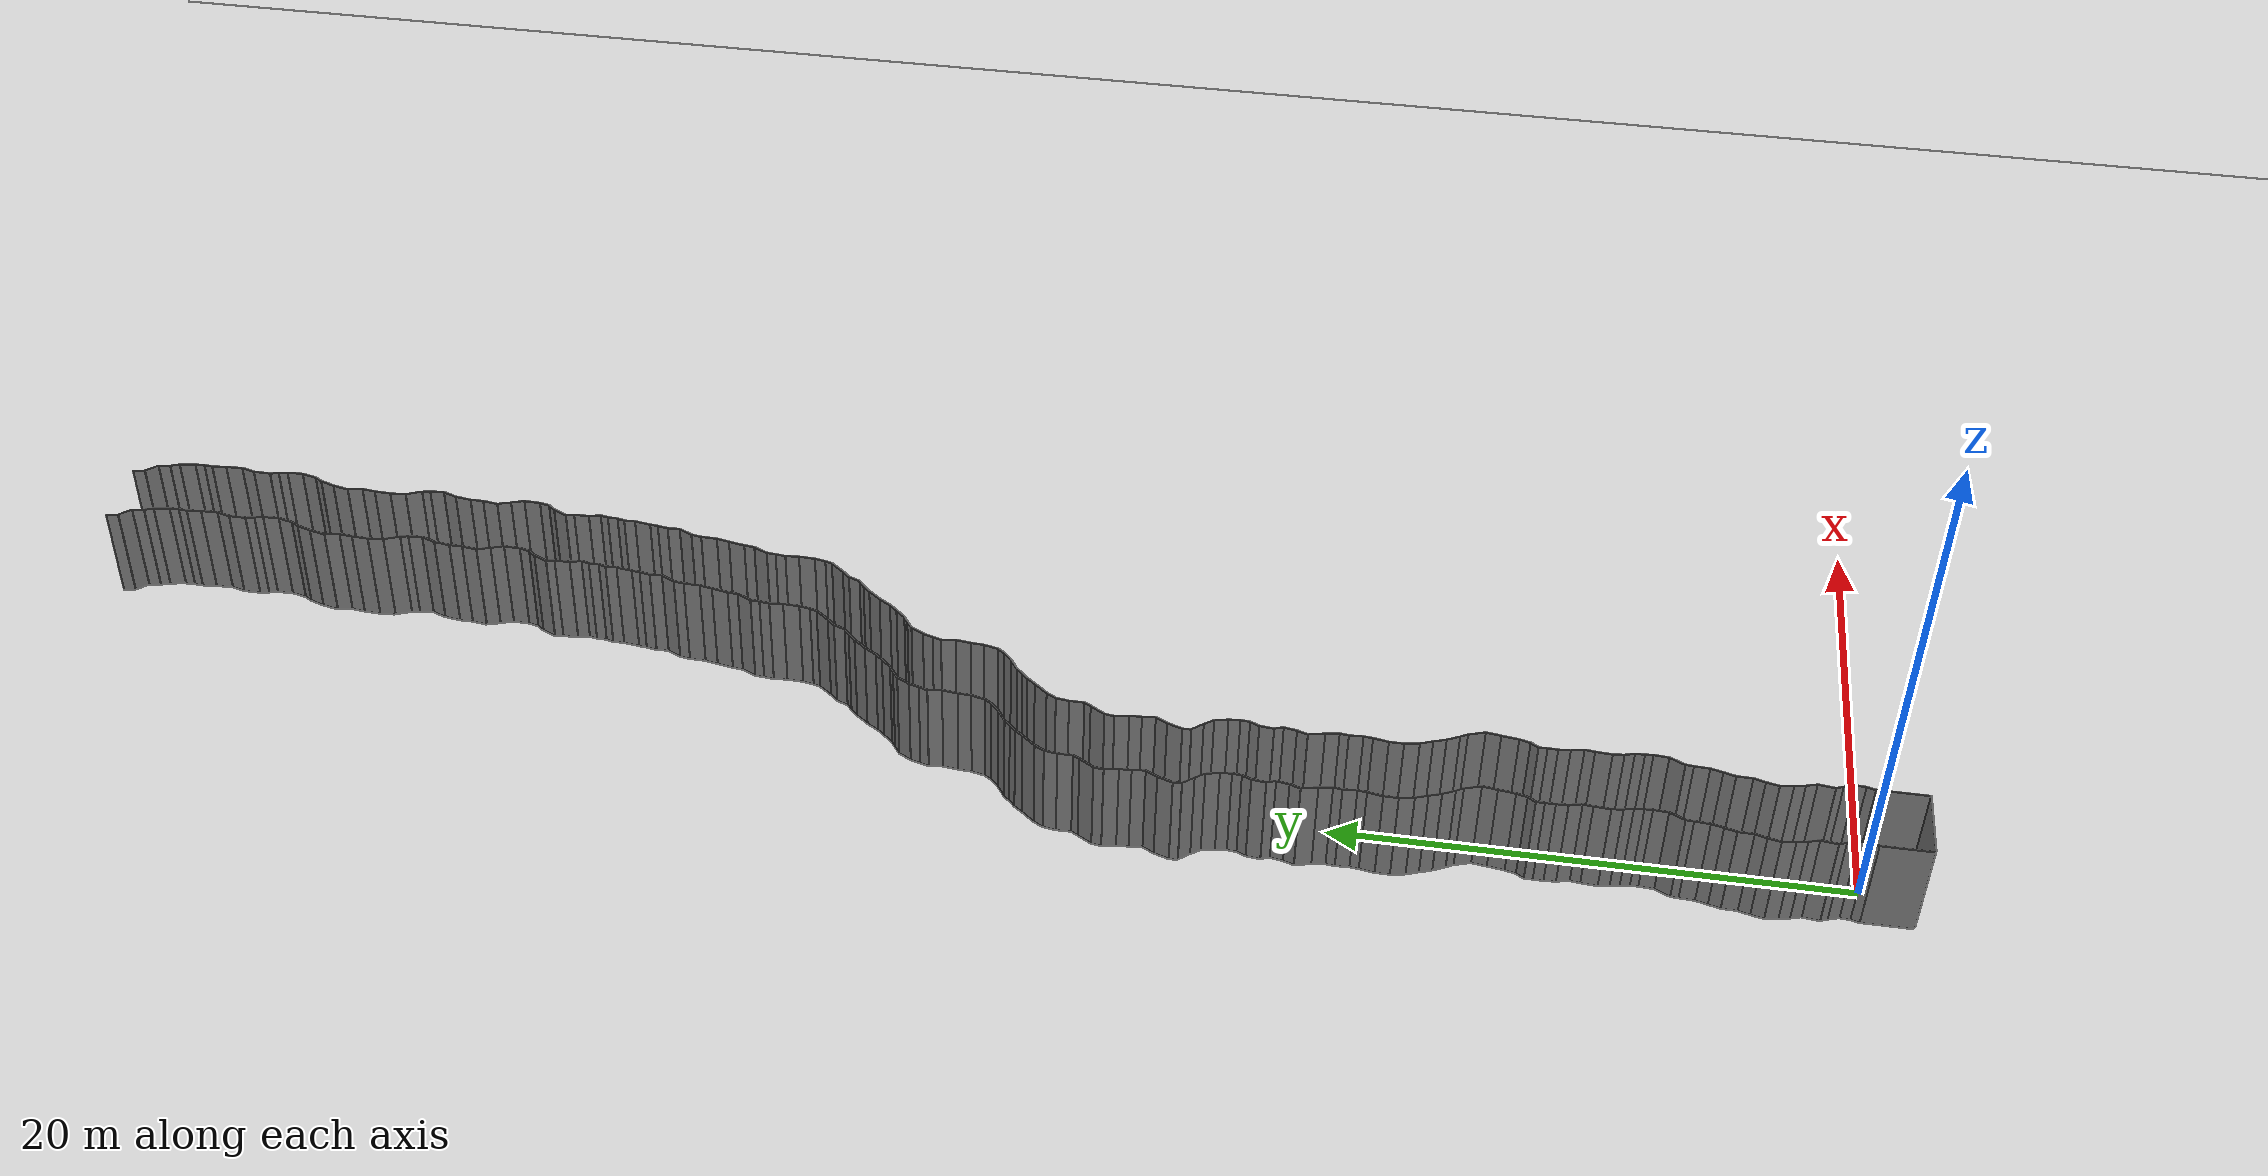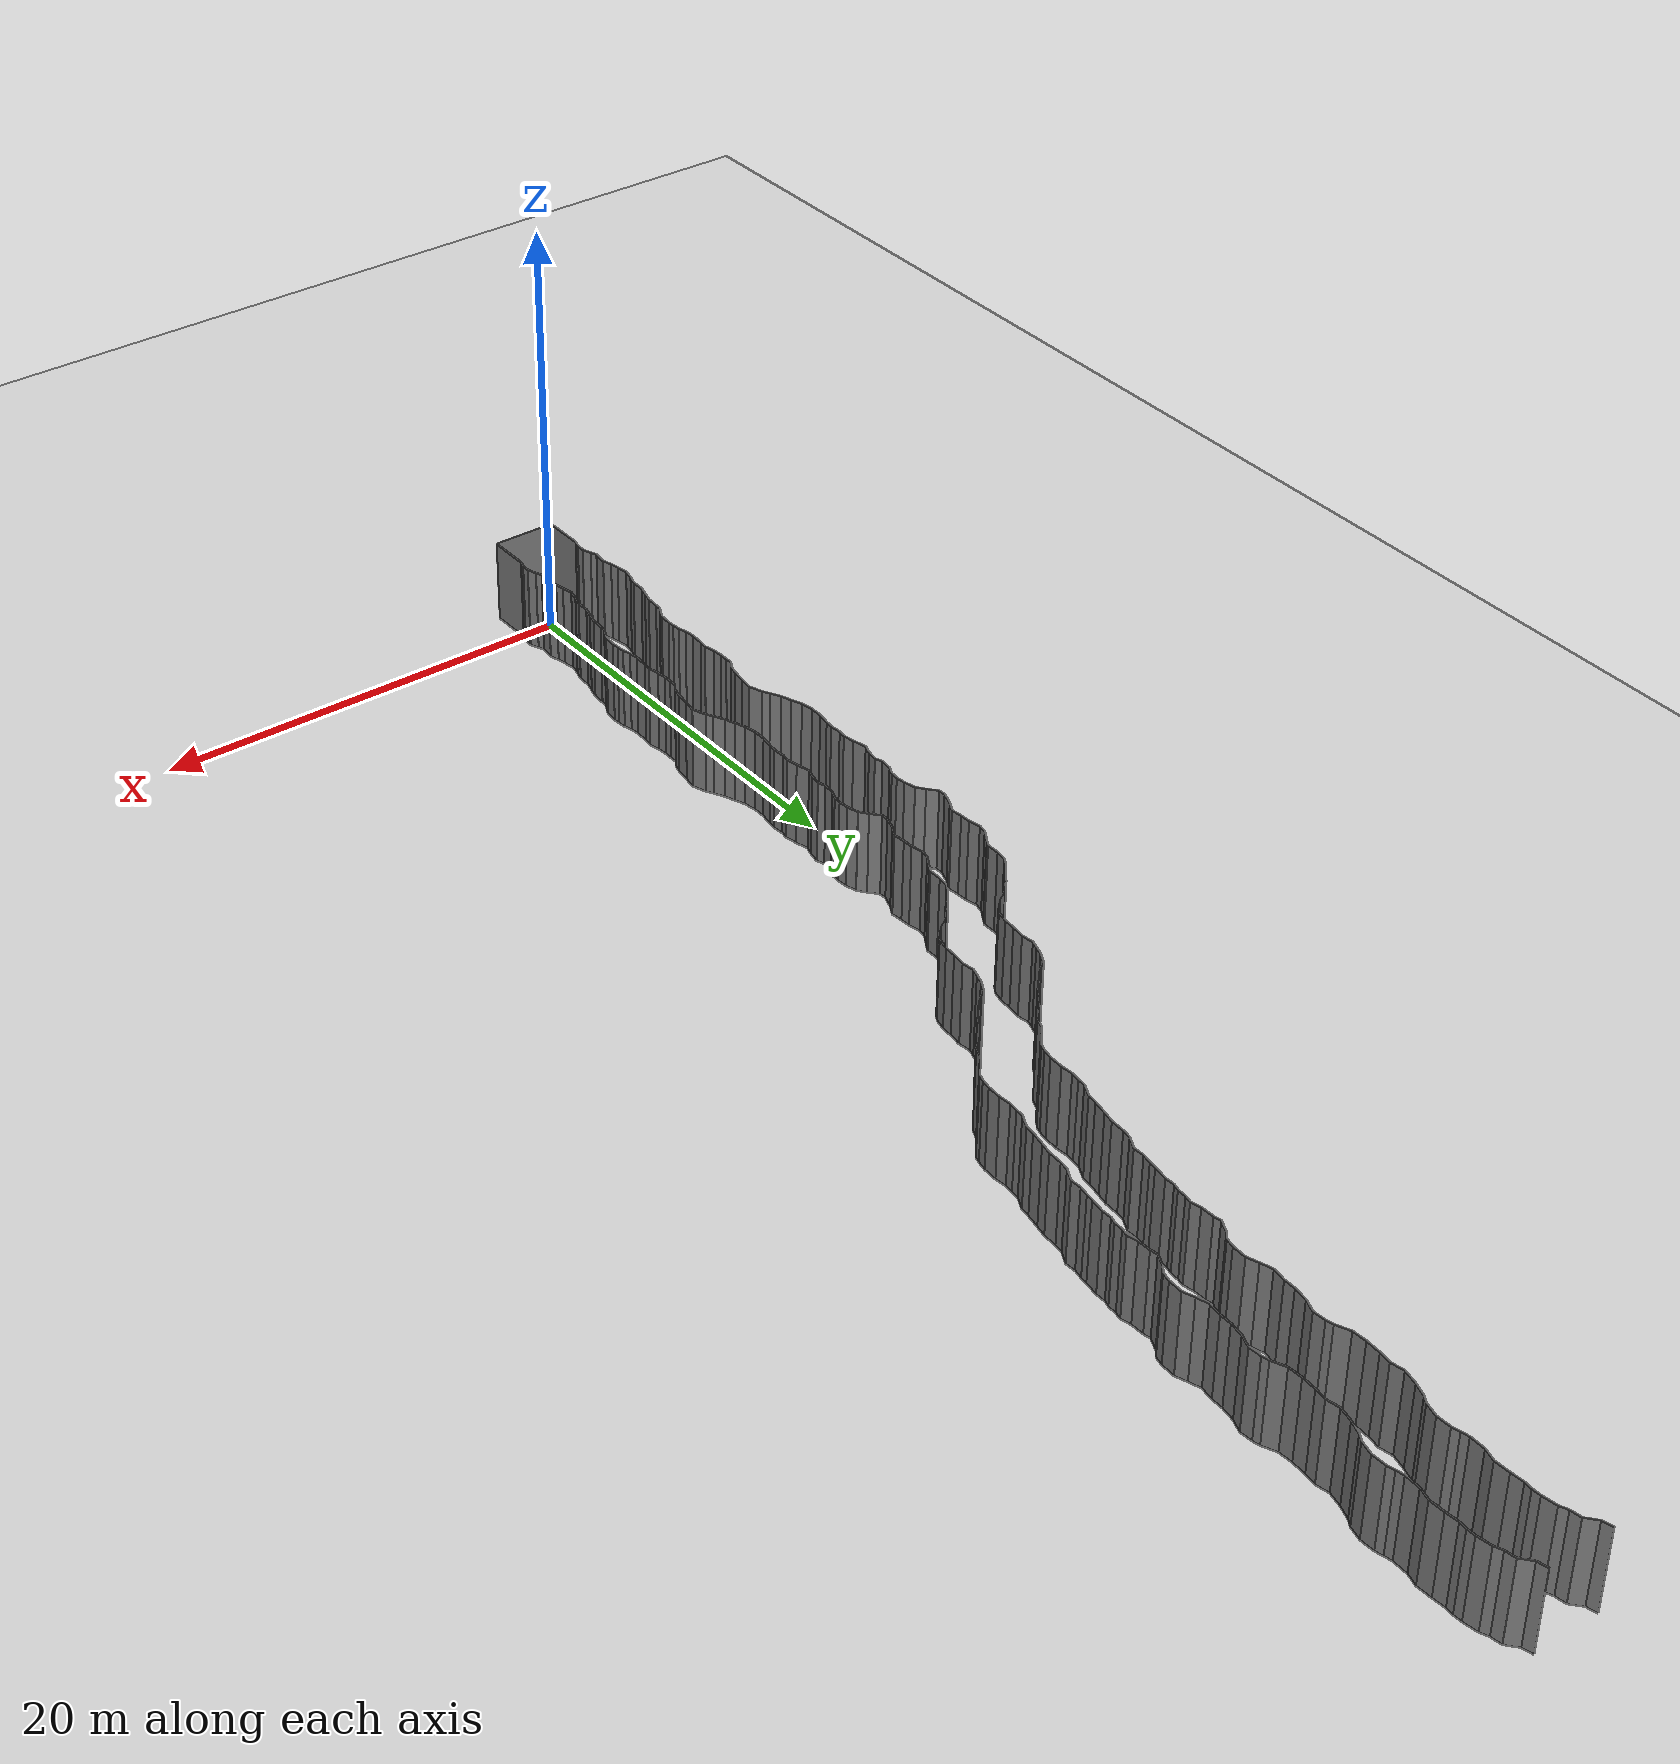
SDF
<sdf version="1.6">
 <world name="default">
  <light name="sun" type="directional">
   <pose>0 0 10 0 -0 0</pose>
   <diffuse>0.8 0.8 0.8 1</diffuse>
   <specular>0.2 0.2 0.2 1</specular>
   <attenuation>
    <range>1000</range>
    <constant>0.9</constant>
    <linear>0.01</linear>
    <quadratic>0.001</quadratic>
   </attenuation>
   <direction>-0.5 0.1 -0.9</direction>
  </light>
  <model name="ground_plane">
   <static>1</static>
   <link name="link">
    <collision name="collision">
     <geometry><plane><normal>0 0 1</normal><size>200 200</size></plane></geometry>
     <surface><friction><ode><mu>100</mu><mu2>50</mu2></ode></friction></surface>
    </collision>
    <visual name="visual">
     <cast_shadows>0</cast_shadows>
     <geometry><plane><normal>0 0 1</normal><size>200 200</size></plane></geometry>
     <material>
      <script><uri>file://media/materials/scripts/gazebo.material</uri><name>Gazebo/Grey</name></script>
     </material>
    </visual>
   </link>
   <pose>0 100 0 0 -0 0</pose>
  </model>
  <gravity>0 0 -9.8</gravity>
  <magnetic_field>6e-06 2.3e-05 -4.2e-05</magnetic_field>
  <atmosphere type="adiabatic"/>
  <physics default="0" name="default_physics" type="ode">
   <max_step_size>0.001</max_step_size>
   <real_time_factor>1</real_time_factor>
   <real_time_update_rate>1000</real_time_update_rate>
  </physics>
  <scene><ambient>0.4 0.4 0.4 1</ambient><background>0.7 0.7 0.7 1</background><shadows>1</shadows></scene>
  <spherical_coordinates>
   <surface_model>EARTH_WGS84</surface_model>
   <latitude_deg>0</latitude_deg>
   <longitude_deg>0</longitude_deg>
   <elevation>0</elevation>
   <heading_deg>0</heading_deg>
  </spherical_coordinates>
  <model name="wall_back">
   <static>1</static>
   <pose>0.0 -2 2 0.0 0 0.0</pose>
   <link name="link">
    <collision name="collision"><geometry><box><size>3 0.02 4</size></box></geometry></collision>
    <visual name="visual">
     <material>
      <script><name>Gazebo/Grey</name><uri>file://media/materials/scripts/gazebo.material</uri></script>
     </material>
     <geometry><box><size>3 0.02 4</size></box></geometry>
    </visual>
   </link>
  </model>
  <model name="wall_left">
   <static>1</static>
   <pose>1.5 -1 2 0 0 0.00</pose>
   <link name="link">
    <collision name="collision"><geometry><box><size>0.02 2 4</size></box></geometry></collision>
    <visual name="visual">
     <material>
      <script><name>Gazebo/Grey</name><uri>file://media/materials/scripts/gazebo.material</uri></script>
     </material>
     <geometry><box><size>0.02 2 4</size></box></geometry>
    </visual>
   </link>
  </model>
  <model name="wall_right">
   <static>1</static>
   <pose>-1.5 -1 2 0 0 0.00</pose>
   <link name="link">
    <collision name="collision"><geometry><box><size>0.02 2 4</size></box></geometry></collision>
    <visual name="visual">
     <material>
      <script><name>Gazebo/Grey</name><uri>file://media/materials/scripts/gazebo.material</uri></script>
     </material>
     <geometry><box><size>0.02 2 4</size></box></geometry>
    </visual>
   </link>
  </model>
  <model name="wall_0">
   <static>1</static>
   <pose>-1.4481622839149968 0.16780448735554085 2 0 0 -0.2996176306300844</pose>
   <link name="link">
    <collision name="collision"><geometry><box><size>0.02 0.351257710438 4</size></box></geometry></collision>
    <visual name="visual">
     <material>
      <script><name>Gazebo/Grey</name><uri>file://media/materials/scripts/gazebo.material</uri></script>
     </material>
     <geometry><box><size>0.02 0.351257710438 4</size></box></geometry>
    </visual>
   </link>
  </model>
  <model name="wall_1">
   <static>1</static>
   <pose>1.5518377160850032 0.16780448735554085 2 0 0 -0.2996176306300844</pose>
   <link name="link">
    <collision name="collision"><geometry><box><size>0.02 0.351257710438 4</size></box></geometry></collision>
    <visual name="visual">
     <material>
      <script><name>Gazebo/Grey</name><uri>file://media/materials/scripts/gazebo.material</uri></script>
     </material>
     <geometry><box><size>0.02 0.351257710438 4</size></box></geometry>
    </visual>
   </link>
  </model>
  <model name="wall_2">
   <static>1</static>
   <pose>-1.3870722859414883 0.5377165227331161 2 0 0 -0.04574706242207418</pose>
   <link name="link">
    <collision name="collision"><geometry><box><size>0.02 0.404638434594 4</size></box></geometry></collision>
    <visual name="visual">
     <material>
      <script><name>Gazebo/Grey</name><uri>file://media/materials/scripts/gazebo.material</uri></script>
     </material>
     <geometry><box><size>0.02 0.404638434594 4</size></box></geometry>
    </visual>
   </link>
  </model>
  <model name="wall_3">
   <static>1</static>
   <pose>1.6129277140585117 0.5377165227331161 2 0 0 -0.04574706242207418</pose>
   <link name="link">
    <collision name="collision"><geometry><box><size>0.02 0.404638434594 4</size></box></geometry></collision>
    <visual name="visual">
     <material>
      <script><name>Gazebo/Grey</name><uri>file://media/materials/scripts/gazebo.material</uri></script>
     </material>
     <geometry><box><size>0.02 0.404638434594 4</size></box></geometry>
    </visual>
   </link>
  </model>
  <model name="wall_4">
   <static>1</static>
   <pose>-1.4535573798969859 0.957338803147812 2 0 0 0.3350652151539047</pose>
   <link name="link">
    <collision name="collision"><geometry><box><size>0.02 0.460646540886 4</size></box></geometry></collision>
    <visual name="visual">
     <material>
      <script><name>Gazebo/Grey</name><uri>file://media/materials/scripts/gazebo.material</uri></script>
     </material>
     <geometry><box><size>0.02 0.460646540886 4</size></box></geometry>
    </visual>
   </link>
  </model>
  <model name="wall_5">
   <static>1</static>
   <pose>1.5464426201030141 0.957338803147812 2 0 0 0.3350652151539047</pose>
   <link name="link">
    <collision name="collision"><geometry><box><size>0.02 0.460646540886 4</size></box></geometry></collision>
    <visual name="visual">
     <material>
      <script><name>Gazebo/Grey</name><uri>file://media/materials/scripts/gazebo.material</uri></script>
     </material>
     <geometry><box><size>0.02 0.460646540886 4</size></box></geometry>
    </visual>
   </link>
  </model>
  <model name="wall_6">
   <static>1</static>
   <pose>-1.5897839429528429 1.3142092592086596 2 0 0 0.40952212110997904</pose>
   <link name="link">
    <collision name="collision"><geometry><box><size>0.02 0.303835215132 4</size></box></geometry></collision>
    <visual name="visual">
     <material>
      <script><name>Gazebo/Grey</name><uri>file://media/materials/scripts/gazebo.material</uri></script>
     </material>
     <geometry><box><size>0.02 0.303835215132 4</size></box></geometry>
    </visual>
   </link>
  </model>
  <model name="wall_7">
   <static>1</static>
   <pose>1.4102160570471571 1.3142092592086596 2 0 0 0.40952212110997904</pose>
   <link name="link">
    <collision name="collision"><geometry><box><size>0.02 0.303835215132 4</size></box></geometry></collision>
    <visual name="visual">
     <material>
      <script><name>Gazebo/Grey</name><uri>file://media/materials/scripts/gazebo.material</uri></script>
     </material>
     <geometry><box><size>0.02 0.303835215132 4</size></box></geometry>
    </visual>
   </link>
  </model>
  <model name="wall_8">
   <static>1</static>
   <pose>-1.6051637080612953 1.7888121610234917 2 0 0 -0.13375236459684292</pose>
   <link name="link">
    <collision name="collision"><geometry><box><size>0.02 0.676536859063 4</size></box></geometry></collision>
    <visual name="visual">
     <material>
      <script><name>Gazebo/Grey</name><uri>file://media/materials/scripts/gazebo.material</uri></script>
     </material>
     <geometry><box><size>0.02 0.676536859063 4</size></box></geometry>
    </visual>
   </link>
  </model>
  <model name="wall_9">
   <static>1</static>
   <pose>1.3948362919387047 1.7888121610234917 2 0 0 -0.13375236459684292</pose>
   <link name="link">
    <collision name="collision"><geometry><box><size>0.02 0.676536859063 4</size></box></geometry></collision>
    <visual name="visual">
     <material>
      <script><name>Gazebo/Grey</name><uri>file://media/materials/scripts/gazebo.material</uri></script>
     </material>
     <geometry><box><size>0.02 0.676536859063 4</size></box></geometry>
    </visual>
   </link>
  </model>
  <model name="wall_10">
   <static>1</static>
   <pose>-1.629949193590575 2.340224699110677 2 0 0 0.31272975462631525</pose>
   <link name="link">
    <collision name="collision"><geometry><box><size>0.02 0.454368841147 4</size></box></geometry></collision>
    <visual name="visual">
     <material>
      <script><name>Gazebo/Grey</name><uri>file://media/materials/scripts/gazebo.material</uri></script>
     </material>
     <geometry><box><size>0.02 0.454368841147 4</size></box></geometry>
    </visual>
   </link>
  </model>
  <model name="wall_11">
   <static>1</static>
   <pose>1.370050806409425 2.340224699110677 2 0 0 0.31272975462631525</pose>
   <link name="link">
    <collision name="collision"><geometry><box><size>0.02 0.454368841147 4</size></box></geometry></collision>
    <visual name="visual">
     <material>
      <script><name>Gazebo/Grey</name><uri>file://media/materials/scripts/gazebo.material</uri></script>
     </material>
     <geometry><box><size>0.02 0.454368841147 4</size></box></geometry>
    </visual>
   </link>
  </model>
  <model name="wall_12">
   <static>1</static>
   <pose>-1.7378465911245706 2.7684076442439713 2 0 0 0.17735878467038635</pose>
   <link name="link">
    <collision name="collision"><geometry><box><size>0.02 0.430792969625 4</size></box></geometry></collision>
    <visual name="visual">
     <material>
      <script><name>Gazebo/Grey</name><uri>file://media/materials/scripts/gazebo.material</uri></script>
     </material>
     <geometry><box><size>0.02 0.430792969625 4</size></box></geometry>
    </visual>
   </link>
  </model>
  <model name="wall_13">
   <static>1</static>
   <pose>1.2621534088754294 2.7684076442439713 2 0 0 0.17735878467038635</pose>
   <link name="link">
    <collision name="collision"><geometry><box><size>0.02 0.430792969625 4</size></box></geometry></collision>
    <visual name="visual">
     <material>
      <script><name>Gazebo/Grey</name><uri>file://media/materials/scripts/gazebo.material</uri></script>
     </material>
     <geometry><box><size>0.02 0.430792969625 4</size></box></geometry>
    </visual>
   </link>
  </model>
  <model name="wall_14">
   <static>1</static>
   <pose>-1.8222864125030118 3.2431577242561613 2 0 0 0.17494080819315336</pose>
   <link name="link">
    <collision name="collision"><geometry><box><size>0.02 0.533609556094 4</size></box></geometry></collision>
    <visual name="visual">
     <material>
      <script><name>Gazebo/Grey</name><uri>file://media/materials/scripts/gazebo.material</uri></script>
     </material>
     <geometry><box><size>0.02 0.533609556094 4</size></box></geometry>
    </visual>
   </link>
  </model>
  <model name="wall_15">
   <static>1</static>
   <pose>1.1777135874969882 3.2431577242561613 2 0 0 0.17494080819315336</pose>
   <link name="link">
    <collision name="collision"><geometry><box><size>0.02 0.533609556094 4</size></box></geometry></collision>
    <visual name="visual">
     <material>
      <script><name>Gazebo/Grey</name><uri>file://media/materials/scripts/gazebo.material</uri></script>
     </material>
     <geometry><box><size>0.02 0.533609556094 4</size></box></geometry>
    </visual>
   </link>
  </model>
  <model name="wall_16">
   <static>1</static>
   <pose>-1.8098432747060365 3.759715212513066 2 0 0 -0.22794116683022206</pose>
   <link name="link">
    <collision name="collision"><geometry><box><size>0.02 0.521129684265 4</size></box></geometry></collision>
    <visual name="visual">
     <material>
      <script><name>Gazebo/Grey</name><uri>file://media/materials/scripts/gazebo.material</uri></script>
     </material>
     <geometry><box><size>0.02 0.521129684265 4</size></box></geometry>
    </visual>
   </link>
  </model>
  <model name="wall_17">
   <static>1</static>
   <pose>1.1901567252939635 3.759715212513066 2 0 0 -0.22794116683022206</pose>
   <link name="link">
    <collision name="collision"><geometry><box><size>0.02 0.521129684265 4</size></box></geometry></collision>
    <visual name="visual">
     <material>
      <script><name>Gazebo/Grey</name><uri>file://media/materials/scripts/gazebo.material</uri></script>
     </material>
     <geometry><box><size>0.02 0.521129684265 4</size></box></geometry>
    </visual>
   </link>
  </model>
  <model name="wall_18">
   <static>1</static>
   <pose>-1.6812586192126178 4.24109299192364 2 0 0 -0.2972456979733456</pose>
   <link name="link">
    <collision name="collision"><geometry><box><size>0.02 0.475978755747 4</size></box></geometry></collision>
    <visual name="visual">
     <material>
      <script><name>Gazebo/Grey</name><uri>file://media/materials/scripts/gazebo.material</uri></script>
     </material>
     <geometry><box><size>0.02 0.475978755747 4</size></box></geometry>
    </visual>
   </link>
  </model>
  <model name="wall_19">
   <static>1</static>
   <pose>1.3187413807873822 4.24109299192364 2 0 0 -0.2972456979733456</pose>
   <link name="link">
    <collision name="collision"><geometry><box><size>0.02 0.475978755747 4</size></box></geometry></collision>
    <visual name="visual">
     <material>
      <script><name>Gazebo/Grey</name><uri>file://media/materials/scripts/gazebo.material</uri></script>
     </material>
     <geometry><box><size>0.02 0.475978755747 4</size></box></geometry>
    </visual>
   </link>
  </model>
  <model name="wall_20">
   <static>1</static>
   <pose>-1.6062313466750713 4.781938812023397 2 0 0 -0.016989123899581415</pose>
   <link name="link">
    <collision name="collision"><geometry><box><size>0.02 0.626676505002 4</size></box></geometry></collision>
    <visual name="visual">
     <material>
      <script><name>Gazebo/Grey</name><uri>file://media/materials/scripts/gazebo.material</uri></script>
     </material>
     <geometry><box><size>0.02 0.626676505002 4</size></box></geometry>
    </visual>
   </link>
  </model>
  <model name="wall_21">
   <static>1</static>
   <pose>1.3937686533249287 4.781938812023397 2 0 0 -0.016989123899581415</pose>
   <link name="link">
    <collision name="collision"><geometry><box><size>0.02 0.626676505002 4</size></box></geometry></collision>
    <visual name="visual">
     <material>
      <script><name>Gazebo/Grey</name><uri>file://media/materials/scripts/gazebo.material</uri></script>
     </material>
     <geometry><box><size>0.02 0.626676505002 4</size></box></geometry>
    </visual>
   </link>
  </model>
  <model name="wall_22">
   <static>1</static>
   <pose>-1.531143853054476 5.331211188134195 2 0 0 -0.2874499627608402</pose>
   <link name="link">
    <collision name="collision"><geometry><box><size>0.02 0.492151693564 4</size></box></geometry></collision>
    <visual name="visual">
     <material>
      <script><name>Gazebo/Grey</name><uri>file://media/materials/scripts/gazebo.material</uri></script>
     </material>
     <geometry><box><size>0.02 0.492151693564 4</size></box></geometry>
    </visual>
   </link>
  </model>
  <model name="wall_23">
   <static>1</static>
   <pose>1.468856146945524 5.331211188134195 2 0 0 -0.2874499627608402</pose>
   <link name="link">
    <collision name="collision"><geometry><box><size>0.02 0.492151693564 4</size></box></geometry></collision>
    <visual name="visual">
     <material>
      <script><name>Gazebo/Grey</name><uri>file://media/materials/scripts/gazebo.material</uri></script>
     </material>
     <geometry><box><size>0.02 0.492151693564 4</size></box></geometry>
    </visual>
   </link>
  </model>
  <model name="wall_24">
   <static>1</static>
   <pose>-1.3978538515136698 5.806062423311456 2 0 0 -0.2599238574407666</pose>
   <link name="link">
    <collision name="collision"><geometry><box><size>0.02 0.494349198365 4</size></box></geometry></collision>
    <visual name="visual">
     <material>
      <script><name>Gazebo/Grey</name><uri>file://media/materials/scripts/gazebo.material</uri></script>
     </material>
     <geometry><box><size>0.02 0.494349198365 4</size></box></geometry>
    </visual>
   </link>
  </model>
  <model name="wall_25">
   <static>1</static>
   <pose>1.6021461484863302 5.806062423311456 2 0 0 -0.2599238574407666</pose>
   <link name="link">
    <collision name="collision"><geometry><box><size>0.02 0.494349198365 4</size></box></geometry></collision>
    <visual name="visual">
     <material>
      <script><name>Gazebo/Grey</name><uri>file://media/materials/scripts/gazebo.material</uri></script>
     </material>
     <geometry><box><size>0.02 0.494349198365 4</size></box></geometry>
    </visual>
   </link>
  </model>
  <model name="wall_26">
   <static>1</static>
   <pose>-1.31751898315386 6.3476481189334155 2 0 0 -0.055471634144057064</pose>
   <link name="link">
    <collision name="collision"><geometry><box><size>0.02 0.606360281936 4</size></box></geometry></collision>
    <visual name="visual">
     <material>
      <script><name>Gazebo/Grey</name><uri>file://media/materials/scripts/gazebo.material</uri></script>
     </material>
     <geometry><box><size>0.02 0.606360281936 4</size></box></geometry>
    </visual>
   </link>
  </model>
  <model name="wall_27">
   <static>1</static>
   <pose>1.68248101684614 6.3476481189334155 2 0 0 -0.055471634144057064</pose>
   <link name="link">
    <collision name="collision"><geometry><box><size>0.02 0.606360281936 4</size></box></geometry></collision>
    <visual name="visual">
     <material>
      <script><name>Gazebo/Grey</name><uri>file://media/materials/scripts/gazebo.material</uri></script>
     </material>
     <geometry><box><size>0.02 0.606360281936 4</size></box></geometry>
    </visual>
   </link>
  </model>
  <model name="wall_28">
   <static>1</static>
   <pose>-1.2881279518696167 6.8042923105226505 2 0 0 -0.0815553701330542</pose>
   <link name="link">
    <collision name="collision"><geometry><box><size>0.02 0.308887457307 4</size></box></geometry></collision>
    <visual name="visual">
     <material>
      <script><name>Gazebo/Grey</name><uri>file://media/materials/scripts/gazebo.material</uri></script>
     </material>
     <geometry><box><size>0.02 0.308887457307 4</size></box></geometry>
    </visual>
   </link>
  </model>
  <model name="wall_29">
   <static>1</static>
   <pose>1.7118720481303833 6.8042923105226505 2 0 0 -0.0815553701330542</pose>
   <link name="link">
    <collision name="collision"><geometry><box><size>0.02 0.308887457307 4</size></box></geometry></collision>
    <visual name="visual">
     <material>
      <script><name>Gazebo/Grey</name><uri>file://media/materials/scripts/gazebo.material</uri></script>
     </material>
     <geometry><box><size>0.02 0.308887457307 4</size></box></geometry>
    </visual>
   </link>
  </model>
  <model name="wall_30">
   <static>1</static>
   <pose>-1.1243460190447574 7.256403919228563 2 0 0 -0.46929139976647033</pose>
   <link name="link">
    <collision name="collision"><geometry><box><size>0.02 0.668650978642 4</size></box></geometry></collision>
    <visual name="visual">
     <material>
      <script><name>Gazebo/Grey</name><uri>file://media/materials/scripts/gazebo.material</uri></script>
     </material>
     <geometry><box><size>0.02 0.668650978642 4</size></box></geometry>
    </visual>
   </link>
  </model>
  <model name="wall_31">
   <static>1</static>
   <pose>1.8756539809552426 7.256403919228563 2 0 0 -0.46929139976647033</pose>
   <link name="link">
    <collision name="collision"><geometry><box><size>0.02 0.668650978642 4</size></box></geometry></collision>
    <visual name="visual">
     <material>
      <script><name>Gazebo/Grey</name><uri>file://media/materials/scripts/gazebo.material</uri></script>
     </material>
     <geometry><box><size>0.02 0.668650978642 4</size></box></geometry>
    </visual>
   </link>
  </model>
  <model name="wall_32">
   <static>1</static>
   <pose>-0.9484871968304259 7.850144005878624 2 0 0 -0.08323780323232564</pose>
   <link name="link">
    <collision name="collision"><geometry><box><size>0.02 0.593171451686 4</size></box></geometry></collision>
    <visual name="visual">
     <material>
      <script><name>Gazebo/Grey</name><uri>file://media/materials/scripts/gazebo.material</uri></script>
     </material>
     <geometry><box><size>0.02 0.593171451686 4</size></box></geometry>
    </visual>
   </link>
  </model>
  <model name="wall_33">
   <static>1</static>
   <pose>2.051512803169574 7.850144005878624 2 0 0 -0.08323780323232564</pose>
   <link name="link">
    <collision name="collision"><geometry><box><size>0.02 0.593171451686 4</size></box></geometry></collision>
    <visual name="visual">
     <material>
      <script><name>Gazebo/Grey</name><uri>file://media/materials/scripts/gazebo.material</uri></script>
     </material>
     <geometry><box><size>0.02 0.593171451686 4</size></box></geometry>
    </visual>
   </link>
  </model>
  <model name="wall_34">
   <static>1</static>
   <pose>-0.9362844113599068 8.302646553862616 2 0 0 0.07919915577153401</pose>
   <link name="link">
    <collision name="collision"><geometry><box><size>0.02 0.314874371414 4</size></box></geometry></collision>
    <visual name="visual">
     <material>
      <script><name>Gazebo/Grey</name><uri>file://media/materials/scripts/gazebo.material</uri></script>
     </material>
     <geometry><box><size>0.02 0.314874371414 4</size></box></geometry>
    </visual>
   </link>
  </model>
  <model name="wall_35">
   <static>1</static>
   <pose>2.0637155886400933 8.302646553862616 2 0 0 0.07919915577153401</pose>
   <link name="link">
    <collision name="collision"><geometry><box><size>0.02 0.314874371414 4</size></box></geometry></collision>
    <visual name="visual">
     <material>
      <script><name>Gazebo/Grey</name><uri>file://media/materials/scripts/gazebo.material</uri></script>
     </material>
     <geometry><box><size>0.02 0.314874371414 4</size></box></geometry>
    </visual>
   </link>
  </model>
  <model name="wall_36">
   <static>1</static>
   <pose>-0.9666049596987792 8.648240813692897 2 0 0 0.09441567546334409</pose>
   <link name="link">
    <collision name="collision"><geometry><box><size>0.02 0.378989118521 4</size></box></geometry></collision>
    <visual name="visual">
     <material>
      <script><name>Gazebo/Grey</name><uri>file://media/materials/scripts/gazebo.material</uri></script>
     </material>
     <geometry><box><size>0.02 0.378989118521 4</size></box></geometry>
    </visual>
   </link>
  </model>
  <model name="wall_37">
   <static>1</static>
   <pose>2.0333950403012206 8.648240813692897 2 0 0 0.09441567546334409</pose>
   <link name="link">
    <collision name="collision"><geometry><box><size>0.02 0.378989118521 4</size></box></geometry></collision>
    <visual name="visual">
     <material>
      <script><name>Gazebo/Grey</name><uri>file://media/materials/scripts/gazebo.material</uri></script>
     </material>
     <geometry><box><size>0.02 0.378989118521 4</size></box></geometry>
    </visual>
   </link>
  </model>
  <model name="wall_38">
   <static>1</static>
   <pose>-1.0373330888710544 9.02675972678839 2 0 0 0.27154443725505956</pose>
   <link name="link">
    <collision name="collision"><geometry><box><size>0.02 0.394180302917 4</size></box></geometry></collision>
    <visual name="visual">
     <material>
      <script><name>Gazebo/Grey</name><uri>file://media/materials/scripts/gazebo.material</uri></script>
     </material>
     <geometry><box><size>0.02 0.394180302917 4</size></box></geometry>
    </visual>
   </link>
  </model>
  <model name="wall_39">
   <static>1</static>
   <pose>1.9626669111289456 9.02675972678839 2 0 0 0.27154443725505956</pose>
   <link name="link">
    <collision name="collision"><geometry><box><size>0.02 0.394180302917 4</size></box></geometry></collision>
    <visual name="visual">
     <material>
      <script><name>Gazebo/Grey</name><uri>file://media/materials/scripts/gazebo.material</uri></script>
     </material>
     <geometry><box><size>0.02 0.394180302917 4</size></box></geometry>
    </visual>
   </link>
  </model>
  <model name="wall_40">
   <static>1</static>
   <pose>-1.1183441626120516 9.435893678911496 2 0 0 0.12767402385074395</pose>
   <link name="link">
    <collision name="collision"><geometry><box><size>0.02 0.442129847013 4</size></box></geometry></collision>
    <visual name="visual">
     <material>
      <script><name>Gazebo/Grey</name><uri>file://media/materials/scripts/gazebo.material</uri></script>
     </material>
     <geometry><box><size>0.02 0.442129847013 4</size></box></geometry>
    </visual>
   </link>
  </model>
  <model name="wall_41">
   <static>1</static>
   <pose>1.8816558373879484 9.435893678911496 2 0 0 0.12767402385074395</pose>
   <link name="link">
    <collision name="collision"><geometry><box><size>0.02 0.442129847013 4</size></box></geometry></collision>
    <visual name="visual">
     <material>
      <script><name>Gazebo/Grey</name><uri>file://media/materials/scripts/gazebo.material</uri></script>
     </material>
     <geometry><box><size>0.02 0.442129847013 4</size></box></geometry>
    </visual>
   </link>
  </model>
  <model name="wall_42">
   <static>1</static>
   <pose>-1.125737672604538 9.982232337623605 2 0 0 -0.06336912984475411</pose>
   <link name="link">
    <collision name="collision"><geometry><box><size>0.02 0.65546169239 4</size></box></geometry></collision>
    <visual name="visual">
     <material>
      <script><name>Gazebo/Grey</name><uri>file://media/materials/scripts/gazebo.material</uri></script>
     </material>
     <geometry><box><size>0.02 0.65546169239 4</size></box></geometry>
    </visual>
   </link>
  </model>
  <model name="wall_43">
   <static>1</static>
   <pose>1.874262327395462 9.982232337623605 2 0 0 -0.06336912984475411</pose>
   <link name="link">
    <collision name="collision"><geometry><box><size>0.02 0.65546169239 4</size></box></geometry></collision>
    <visual name="visual">
     <material>
      <script><name>Gazebo/Grey</name><uri>file://media/materials/scripts/gazebo.material</uri></script>
     </material>
     <geometry><box><size>0.02 0.65546169239 4</size></box></geometry>
    </visual>
   </link>
  </model>
  <model name="wall_44">
   <static>1</static>
   <pose>-1.0807867780076557 10.507442569947084 2 0 0 -0.12151959194990355</pose>
   <link name="link">
    <collision name="collision"><geometry><box><size>0.02 0.399218388871 4</size></box></geometry></collision>
    <visual name="visual">
     <material>
      <script><name>Gazebo/Grey</name><uri>file://media/materials/scripts/gazebo.material</uri></script>
     </material>
     <geometry><box><size>0.02 0.399218388871 4</size></box></geometry>
    </visual>
   </link>
  </model>
  <model name="wall_45">
   <static>1</static>
   <pose>1.9192132219923443 10.507442569947084 2 0 0 -0.12151959194990355</pose>
   <link name="link">
    <collision name="collision"><geometry><box><size>0.02 0.399218388871 4</size></box></geometry></collision>
    <visual name="visual">
     <material>
      <script><name>Gazebo/Grey</name><uri>file://media/materials/scripts/gazebo.material</uri></script>
     </material>
     <geometry><box><size>0.02 0.399218388871 4</size></box></geometry>
    </visual>
   </link>
  </model>
  <model name="wall_46">
   <static>1</static>
   <pose>-1.1150622967381114 10.9606910244499 2 0 0 0.2253113913435937</pose>
   <link name="link">
    <collision name="collision"><geometry><box><size>0.02 0.523453017329 4</size></box></geometry></collision>
    <visual name="visual">
     <material>
      <script><name>Gazebo/Grey</name><uri>file://media/materials/scripts/gazebo.material</uri></script>
     </material>
     <geometry><box><size>0.02 0.523453017329 4</size></box></geometry>
    </visual>
   </link>
  </model>
  <model name="wall_47">
   <static>1</static>
   <pose>1.8849377032618886 10.9606910244499 2 0 0 0.2253113913435937</pose>
   <link name="link">
    <collision name="collision"><geometry><box><size>0.02 0.523453017329 4</size></box></geometry></collision>
    <visual name="visual">
     <material>
      <script><name>Gazebo/Grey</name><uri>file://media/materials/scripts/gazebo.material</uri></script>
     </material>
     <geometry><box><size>0.02 0.523453017329 4</size></box></geometry>
    </visual>
   </link>
  </model>
  <model name="wall_48">
   <static>1</static>
   <pose>-1.1928911129790516 11.448885990914029 2 0 0 0.08285525769127004</pose>
   <link name="link">
    <collision name="collision"><geometry><box><size>0.02 0.467772115079 4</size></box></geometry></collision>
    <visual name="visual">
     <material>
      <script><name>Gazebo/Grey</name><uri>file://media/materials/scripts/gazebo.material</uri></script>
     </material>
     <geometry><box><size>0.02 0.467772115079 4</size></box></geometry>
    </visual>
   </link>
  </model>
  <model name="wall_49">
   <static>1</static>
   <pose>1.8071088870209484 11.448885990914029 2 0 0 0.08285525769127004</pose>
   <link name="link">
    <collision name="collision"><geometry><box><size>0.02 0.467772115079 4</size></box></geometry></collision>
    <visual name="visual">
     <material>
      <script><name>Gazebo/Grey</name><uri>file://media/materials/scripts/gazebo.material</uri></script>
     </material>
     <geometry><box><size>0.02 0.467772115079 4</size></box></geometry>
    </visual>
   </link>
  </model>
  <model name="wall_50">
   <static>1</static>
   <pose>-1.208191218170536 11.881205040745478 2 0 0 -0.02035712674399414</pose>
   <link name="link">
    <collision name="collision"><geometry><box><size>0.02 0.39855327246 4</size></box></geometry></collision>
    <visual name="visual">
     <material>
      <script><name>Gazebo/Grey</name><uri>file://media/materials/scripts/gazebo.material</uri></script>
     </material>
     <geometry><box><size>0.02 0.39855327246 4</size></box></geometry>
    </visual>
   </link>
  </model>
  <model name="wall_51">
   <static>1</static>
   <pose>1.791808781829464 11.881205040745478 2 0 0 -0.02035712674399414</pose>
   <link name="link">
    <collision name="collision"><geometry><box><size>0.02 0.39855327246 4</size></box></geometry></collision>
    <visual name="visual">
     <material>
      <script><name>Gazebo/Grey</name><uri>file://media/materials/scripts/gazebo.material</uri></script>
     </material>
     <geometry><box><size>0.02 0.39855327246 4</size></box></geometry>
    </visual>
   </link>
  </model>
  <model name="wall_52">
   <static>1</static>
   <pose>-1.2072234631017604 12.246882023853656 2 0 0 0.018554912564470328</pose>
   <link name="link">
    <collision name="collision"><geometry><box><size>0.02 0.3329405852 4</size></box></geometry></collision>
    <visual name="visual">
     <material>
      <script><name>Gazebo/Grey</name><uri>file://media/materials/scripts/gazebo.material</uri></script>
     </material>
     <geometry><box><size>0.02 0.3329405852 4</size></box></geometry>
    </visual>
   </link>
  </model>
  <model name="wall_53">
   <static>1</static>
   <pose>1.7927765368982396 12.246882023853656 2 0 0 0.018554912564470328</pose>
   <link name="link">
    <collision name="collision"><geometry><box><size>0.02 0.3329405852 4</size></box></geometry></collision>
    <visual name="visual">
     <material>
      <script><name>Gazebo/Grey</name><uri>file://media/materials/scripts/gazebo.material</uri></script>
     </material>
     <geometry><box><size>0.02 0.3329405852 4</size></box></geometry>
    </visual>
   </link>
  </model>
  <model name="wall_54">
   <static>1</static>
   <pose>-1.1042760674856207 12.56503613000004 2 0 0 -0.6100059943093987</pose>
   <link name="link">
    <collision name="collision"><geometry><box><size>0.02 0.370190866386 4</size></box></geometry></collision>
    <visual name="visual">
     <material>
      <script><name>Gazebo/Grey</name><uri>file://media/materials/scripts/gazebo.material</uri></script>
     </material>
     <geometry><box><size>0.02 0.370190866386 4</size></box></geometry>
    </visual>
   </link>
  </model>
  <model name="wall_55">
   <static>1</static>
   <pose>1.8957239325143793 12.56503613000004 2 0 0 -0.6100059943093987</pose>
   <link name="link">
    <collision name="collision"><geometry><box><size>0.02 0.370190866386 4</size></box></geometry></collision>
    <visual name="visual">
     <material>
      <script><name>Gazebo/Grey</name><uri>file://media/materials/scripts/gazebo.material</uri></script>
     </material>
     <geometry><box><size>0.02 0.370190866386 4</size></box></geometry>
    </visual>
   </link>
  </model>
  <model name="wall_56">
   <static>1</static>
   <pose>-0.9397064069056849 12.932126643532035 2 0 0 -0.2653621705661002</pose>
   <link name="link">
    <collision name="collision"><geometry><box><size>0.02 0.446380484851 4</size></box></geometry></collision>
    <visual name="visual">
     <material>
      <script><name>Gazebo/Grey</name><uri>file://media/materials/scripts/gazebo.material</uri></script>
     </material>
     <geometry><box><size>0.02 0.446380484851 4</size></box></geometry>
    </visual>
   </link>
  </model>
  <model name="wall_57">
   <static>1</static>
   <pose>2.060293593094315 12.932126643532035 2 0 0 -0.2653621705661002</pose>
   <link name="link">
    <collision name="collision"><geometry><box><size>0.02 0.446380484851 4</size></box></geometry></collision>
    <visual name="visual">
     <material>
      <script><name>Gazebo/Grey</name><uri>file://media/materials/scripts/gazebo.material</uri></script>
     </material>
     <geometry><box><size>0.02 0.446380484851 4</size></box></geometry>
    </visual>
   </link>
  </model>
  <model name="wall_58">
   <static>1</static>
   <pose>-0.8318482900212258 13.485929932124142 2 0 0 -0.14472811307809</pose>
   <link name="link">
    <collision name="collision"><geometry><box><size>0.02 0.684001619739 4</size></box></geometry></collision>
    <visual name="visual">
     <material>
      <script><name>Gazebo/Grey</name><uri>file://media/materials/scripts/gazebo.material</uri></script>
     </material>
     <geometry><box><size>0.02 0.684001619739 4</size></box></geometry>
    </visual>
   </link>
  </model>
  <model name="wall_59">
   <static>1</static>
   <pose>2.1681517099787744 13.485929932124142 2 0 0 -0.14472811307809</pose>
   <link name="link">
    <collision name="collision"><geometry><box><size>0.02 0.684001619739 4</size></box></geometry></collision>
    <visual name="visual">
     <material>
      <script><name>Gazebo/Grey</name><uri>file://media/materials/scripts/gazebo.material</uri></script>
     </material>
     <geometry><box><size>0.02 0.684001619739 4</size></box></geometry>
    </visual>
   </link>
  </model>
  <model name="wall_60">
   <static>1</static>
   <pose>-0.7390169700668391 14.12154388235925 2 0 0 -0.14536197285969535</pose>
   <link name="link">
    <collision name="collision"><geometry><box><size>0.02 0.600712806068 4</size></box></geometry></collision>
    <visual name="visual">
     <material>
      <script><name>Gazebo/Grey</name><uri>file://media/materials/scripts/gazebo.material</uri></script>
     </material>
     <geometry><box><size>0.02 0.600712806068 4</size></box></geometry>
    </visual>
   </link>
  </model>
  <model name="wall_61">
   <static>1</static>
   <pose>2.260983029933161 14.12154388235925 2 0 0 -0.14536197285969535</pose>
   <link name="link">
    <collision name="collision"><geometry><box><size>0.02 0.600712806068 4</size></box></geometry></collision>
    <visual name="visual">
     <material>
      <script><name>Gazebo/Grey</name><uri>file://media/materials/scripts/gazebo.material</uri></script>
     </material>
     <geometry><box><size>0.02 0.600712806068 4</size></box></geometry>
    </visual>
   </link>
  </model>
  <model name="wall_62">
   <static>1</static>
   <pose>-0.8118996984164512 14.747489583500007 2 0 0 0.3402596685851604</pose>
   <link name="link">
    <collision name="collision"><geometry><box><size>0.02 0.69750321887 4</size></box></geometry></collision>
    <visual name="visual">
     <material>
      <script><name>Gazebo/Grey</name><uri>file://media/materials/scripts/gazebo.material</uri></script>
     </material>
     <geometry><box><size>0.02 0.69750321887 4</size></box></geometry>
    </visual>
   </link>
  </model>
  <model name="wall_63">
   <static>1</static>
   <pose>2.1881003015835487 14.747489583500007 2 0 0 0.3402596685851604</pose>
   <link name="link">
    <collision name="collision"><geometry><box><size>0.02 0.69750321887 4</size></box></geometry></collision>
    <visual name="visual">
     <material>
      <script><name>Gazebo/Grey</name><uri>file://media/materials/scripts/gazebo.material</uri></script>
     </material>
     <geometry><box><size>0.02 0.69750321887 4</size></box></geometry>
    </visual>
   </link>
  </model>
  <model name="wall_64">
   <static>1</static>
   <pose>-1.0164430715528123 15.221188934079931 2 0 0 0.5464266062400854</pose>
   <link name="link">
    <collision name="collision"><geometry><box><size>0.02 0.339289764561 4</size></box></geometry></collision>
    <visual name="visual">
     <material>
      <script><name>Gazebo/Grey</name><uri>file://media/materials/scripts/gazebo.material</uri></script>
     </material>
     <geometry><box><size>0.02 0.339289764561 4</size></box></geometry>
    </visual>
   </link>
  </model>
  <model name="wall_65">
   <static>1</static>
   <pose>1.9835569284471877 15.221188934079931 2 0 0 0.5464266062400854</pose>
   <link name="link">
    <collision name="collision"><geometry><box><size>0.02 0.339289764561 4</size></box></geometry></collision>
    <visual name="visual">
     <material>
      <script><name>Gazebo/Grey</name><uri>file://media/materials/scripts/gazebo.material</uri></script>
     </material>
     <geometry><box><size>0.02 0.339289764561 4</size></box></geometry>
    </visual>
   </link>
  </model>
  <model name="wall_66">
   <static>1</static>
   <pose>-1.2282635963553432 15.610428997550057 2 0 0 0.46860567202167186</pose>
   <link name="link">
    <collision name="collision"><geometry><box><size>0.02 0.5476306012 4</size></box></geometry></collision>
    <visual name="visual">
     <material>
      <script><name>Gazebo/Grey</name><uri>file://media/materials/scripts/gazebo.material</uri></script>
     </material>
     <geometry><box><size>0.02 0.5476306012 4</size></box></geometry>
    </visual>
   </link>
  </model>
  <model name="wall_67">
   <static>1</static>
   <pose>1.7717364036446568 15.610428997550057 2 0 0 0.46860567202167186</pose>
   <link name="link">
    <collision name="collision"><geometry><box><size>0.02 0.5476306012 4</size></box></geometry></collision>
    <visual name="visual">
     <material>
      <script><name>Gazebo/Grey</name><uri>file://media/materials/scripts/gazebo.material</uri></script>
     </material>
     <geometry><box><size>0.02 0.5476306012 4</size></box></geometry>
    </visual>
   </link>
  </model>
  <model name="wall_68">
   <static>1</static>
   <pose>-1.4414523322096484 16.101758550467835 2 0 0 0.3476704117823307</pose>
   <link name="link">
    <collision name="collision"><geometry><box><size>0.02 0.525505205164 4</size></box></geometry></collision>
    <visual name="visual">
     <material>
      <script><name>Gazebo/Grey</name><uri>file://media/materials/scripts/gazebo.material</uri></script>
     </material>
     <geometry><box><size>0.02 0.525505205164 4</size></box></geometry>
    </visual>
   </link>
  </model>
  <model name="wall_69">
   <static>1</static>
   <pose>1.5585476677903516 16.101758550467835 2 0 0 0.3476704117823307</pose>
   <link name="link">
    <collision name="collision"><geometry><box><size>0.02 0.525505205164 4</size></box></geometry></collision>
    <visual name="visual">
     <material>
      <script><name>Gazebo/Grey</name><uri>file://media/materials/scripts/gazebo.material</uri></script>
     </material>
     <geometry><box><size>0.02 0.525505205164 4</size></box></geometry>
    </visual>
   </link>
  </model>
  <model name="wall_70">
   <static>1</static>
   <pose>-1.6259843733317463 16.592851796713802 2 0 0 0.371237261087657</pose>
   <link name="link">
    <collision name="collision"><geometry><box><size>0.02 0.523804794484 4</size></box></geometry></collision>
    <visual name="visual">
     <material>
      <script><name>Gazebo/Grey</name><uri>file://media/materials/scripts/gazebo.material</uri></script>
     </material>
     <geometry><box><size>0.02 0.523804794484 4</size></box></geometry>
    </visual>
   </link>
  </model>
  <model name="wall_71">
   <static>1</static>
   <pose>1.3740156266682537 16.592851796713802 2 0 0 0.371237261087657</pose>
   <link name="link">
    <collision name="collision"><geometry><box><size>0.02 0.523804794484 4</size></box></geometry></collision>
    <visual name="visual">
     <material>
      <script><name>Gazebo/Grey</name><uri>file://media/materials/scripts/gazebo.material</uri></script>
     </material>
     <geometry><box><size>0.02 0.523804794484 4</size></box></geometry>
    </visual>
   </link>
  </model>
  <model name="wall_72">
   <static>1</static>
   <pose>-1.772603717466998 17.128168511089463 2 0 0 0.17537587751921788</pose>
   <link name="link">
    <collision name="collision"><geometry><box><size>0.02 0.591584931626 4</size></box></geometry></collision>
    <visual name="visual">
     <material>
      <script><name>Gazebo/Grey</name><uri>file://media/materials/scripts/gazebo.material</uri></script>
     </material>
     <geometry><box><size>0.02 0.591584931626 4</size></box></geometry>
    </visual>
   </link>
  </model>
  <model name="wall_73">
   <static>1</static>
   <pose>1.227396282533002 17.128168511089463 2 0 0 0.17537587751921788</pose>
   <link name="link">
    <collision name="collision"><geometry><box><size>0.02 0.591584931626 4</size></box></geometry></collision>
    <visual name="visual">
     <material>
      <script><name>Gazebo/Grey</name><uri>file://media/materials/scripts/gazebo.material</uri></script>
     </material>
     <geometry><box><size>0.02 0.591584931626 4</size></box></geometry>
    </visual>
   </link>
  </model>
  <model name="wall_74">
   <static>1</static>
   <pose>-1.8227342773542958 17.706862946428046 2 0 0 -0.005144680229264741</pose>
   <link name="link">
    <collision name="collision"><geometry><box><size>0.02 0.574885852878 4</size></box></geometry></collision>
    <visual name="visual">
     <material>
      <script><name>Gazebo/Grey</name><uri>file://media/materials/scripts/gazebo.material</uri></script>
     </material>
     <geometry><box><size>0.02 0.574885852878 4</size></box></geometry>
    </visual>
   </link>
  </model>
  <model name="wall_75">
   <static>1</static>
   <pose>1.1772657226457042 17.706862946428046 2 0 0 -0.005144680229264741</pose>
   <link name="link">
    <collision name="collision"><geometry><box><size>0.02 0.574885852878 4</size></box></geometry></collision>
    <visual name="visual">
     <material>
      <script><name>Gazebo/Grey</name><uri>file://media/materials/scripts/gazebo.material</uri></script>
     </material>
     <geometry><box><size>0.02 0.574885852878 4</size></box></geometry>
    </visual>
   </link>
  </model>
  <model name="wall_76">
   <static>1</static>
   <pose>-1.7670484953008045 18.296011256512756 2 0 0 -0.17776973445349756</pose>
   <link name="link">
    <collision name="collision"><geometry><box><size>0.02 0.613080194735 4</size></box></geometry></collision>
    <visual name="visual">
     <material>
      <script><name>Gazebo/Grey</name><uri>file://media/materials/scripts/gazebo.material</uri></script>
     </material>
     <geometry><box><size>0.02 0.613080194735 4</size></box></geometry>
    </visual>
   </link>
  </model>
  <model name="wall_77">
   <static>1</static>
   <pose>1.2329515046991955 18.296011256512756 2 0 0 -0.17776973445349756</pose>
   <link name="link">
    <collision name="collision"><geometry><box><size>0.02 0.613080194735 4</size></box></geometry></collision>
    <visual name="visual">
     <material>
      <script><name>Gazebo/Grey</name><uri>file://media/materials/scripts/gazebo.material</uri></script>
     </material>
     <geometry><box><size>0.02 0.613080194735 4</size></box></geometry>
    </visual>
   </link>
  </model>
  <model name="wall_78">
   <static>1</static>
   <pose>-1.691616229469067 18.779358773120155 2 0 0 -0.11632705927384102</pose>
   <link name="link">
    <collision name="collision"><geometry><box><size>0.02 0.36574852035 4</size></box></geometry></collision>
    <visual name="visual">
     <material>
      <script><name>Gazebo/Grey</name><uri>file://media/materials/scripts/gazebo.material</uri></script>
     </material>
     <geometry><box><size>0.02 0.36574852035 4</size></box></geometry>
    </visual>
   </link>
  </model>
  <model name="wall_79">
   <static>1</static>
   <pose>1.308383770530933 18.779358773120155 2 0 0 -0.11632705927384102</pose>
   <link name="link">
    <collision name="collision"><geometry><box><size>0.02 0.36574852035 4</size></box></geometry></collision>
    <visual name="visual">
     <material>
      <script><name>Gazebo/Grey</name><uri>file://media/materials/scripts/gazebo.material</uri></script>
     </material>
     <geometry><box><size>0.02 0.36574852035 4</size></box></geometry>
    </visual>
   </link>
  </model>
  <model name="wall_80">
   <static>1</static>
   <pose>-1.6900351141904346 19.23614180279817 2 0 0 0.07127481586271396</pose>
   <link name="link">
    <collision name="collision"><geometry><box><size>0.02 0.551690128582 4</size></box></geometry></collision>
    <visual name="visual">
     <material>
      <script><name>Gazebo/Grey</name><uri>file://media/materials/scripts/gazebo.material</uri></script>
     </material>
     <geometry><box><size>0.02 0.551690128582 4</size></box></geometry>
    </visual>
   </link>
  </model>
  <model name="wall_81">
   <static>1</static>
   <pose>1.3099648858095654 19.23614180279817 2 0 0 0.07127481586271396</pose>
   <link name="link">
    <collision name="collision"><geometry><box><size>0.02 0.551690128582 4</size></box></geometry></collision>
    <visual name="visual">
     <material>
      <script><name>Gazebo/Grey</name><uri>file://media/materials/scripts/gazebo.material</uri></script>
     </material>
     <geometry><box><size>0.02 0.551690128582 4</size></box></geometry>
    </visual>
   </link>
  </model>
  <model name="wall_82">
   <static>1</static>
   <pose>-1.6828735805820336 19.68751470379717 2 0 0 -0.15095080142722841</pose>
   <link name="link">
    <collision name="collision"><geometry><box><size>0.02 0.356510443068 4</size></box></geometry></collision>
    <visual name="visual">
     <material>
      <script><name>Gazebo/Grey</name><uri>file://media/materials/scripts/gazebo.material</uri></script>
     </material>
     <geometry><box><size>0.02 0.356510443068 4</size></box></geometry>
    </visual>
   </link>
  </model>
  <model name="wall_83">
   <static>1</static>
   <pose>1.3171264194179664 19.68751470379717 2 0 0 -0.15095080142722841</pose>
   <link name="link">
    <collision name="collision"><geometry><box><size>0.02 0.356510443068 4</size></box></geometry></collision>
    <visual name="visual">
     <material>
      <script><name>Gazebo/Grey</name><uri>file://media/materials/scripts/gazebo.material</uri></script>
     </material>
     <geometry><box><size>0.02 0.356510443068 4</size></box></geometry>
    </visual>
   </link>
  </model>
  <model name="wall_84">
   <static>1</static>
   <pose>-1.7035136882421782 20.132669639604867 2 0 0 0.1746294509358249</pose>
   <link name="link">
    <collision name="collision"><geometry><box><size>0.02 0.546160025983 4</size></box></geometry></collision>
    <visual name="visual">
     <material>
      <script><name>Gazebo/Grey</name><uri>file://media/materials/scripts/gazebo.material</uri></script>
     </material>
     <geometry><box><size>0.02 0.546160025983 4</size></box></geometry>
    </visual>
   </link>
  </model>
  <model name="wall_85">
   <static>1</static>
   <pose>1.2964863117578218 20.132669639604867 2 0 0 0.1746294509358249</pose>
   <link name="link">
    <collision name="collision"><geometry><box><size>0.02 0.546160025983 4</size></box></geometry></collision>
    <visual name="visual">
     <material>
      <script><name>Gazebo/Grey</name><uri>file://media/materials/scripts/gazebo.material</uri></script>
     </material>
     <geometry><box><size>0.02 0.546160025983 4</size></box></geometry>
    </visual>
   </link>
  </model>
  <model name="wall_86">
   <static>1</static>
   <pose>-1.829740497074928 20.723104938696643 2 0 0 0.24030073884697628</pose>
   <link name="link">
    <collision name="collision"><geometry><box><size>0.02 0.662039887014 4</size></box></geometry></collision>
    <visual name="visual">
     <material>
      <script><name>Gazebo/Grey</name><uri>file://media/materials/scripts/gazebo.material</uri></script>
     </material>
     <geometry><box><size>0.02 0.662039887014 4</size></box></geometry>
    </visual>
   </link>
  </model>
  <model name="wall_87">
   <static>1</static>
   <pose>1.170259502925072 20.723104938696643 2 0 0 0.24030073884697628</pose>
   <link name="link">
    <collision name="collision"><geometry><box><size>0.02 0.662039887014 4</size></box></geometry></collision>
    <visual name="visual">
     <material>
      <script><name>Gazebo/Grey</name><uri>file://media/materials/scripts/gazebo.material</uri></script>
     </material>
     <geometry><box><size>0.02 0.662039887014 4</size></box></geometry>
    </visual>
   </link>
  </model>
  <model name="wall_88">
   <static>1</static>
   <pose>-1.832279762551081 21.256791881495644 2 0 0 -0.3449609928496179</pose>
   <link name="link">
    <collision name="collision"><geometry><box><size>0.02 0.450921133866 4</size></box></geometry></collision>
    <visual name="visual">
     <material>
      <script><name>Gazebo/Grey</name><uri>file://media/materials/scripts/gazebo.material</uri></script>
     </material>
     <geometry><box><size>0.02 0.450921133866 4</size></box></geometry>
    </visual>
   </link>
  </model>
  <model name="wall_89">
   <static>1</static>
   <pose>1.167720237448919 21.256791881495644 2 0 0 -0.3449609928496179</pose>
   <link name="link">
    <collision name="collision"><geometry><box><size>0.02 0.450921133866 4</size></box></geometry></collision>
    <visual name="visual">
     <material>
      <script><name>Gazebo/Grey</name><uri>file://media/materials/scripts/gazebo.material</uri></script>
     </material>
     <geometry><box><size>0.02 0.450921133866 4</size></box></geometry>
    </visual>
   </link>
  </model>
  <model name="wall_90">
   <static>1</static>
   <pose>-1.7093550446414636 21.726342850405377 2 0 0 -0.17943208854441056</pose>
   <link name="link">
    <collision name="collision"><geometry><box><size>0.02 0.523144150415 4</size></box></geometry></collision>
    <visual name="visual">
     <material>
      <script><name>Gazebo/Grey</name><uri>file://media/materials/scripts/gazebo.material</uri></script>
     </material>
     <geometry><box><size>0.02 0.523144150415 4</size></box></geometry>
    </visual>
   </link>
  </model>
  <model name="wall_91">
   <static>1</static>
   <pose>1.2906449553585364 21.726342850405377 2 0 0 -0.17943208854441056</pose>
   <link name="link">
    <collision name="collision"><geometry><box><size>0.02 0.523144150415 4</size></box></geometry></collision>
    <visual name="visual">
     <material>
      <script><name>Gazebo/Grey</name><uri>file://media/materials/scripts/gazebo.material</uri></script>
     </material>
     <geometry><box><size>0.02 0.523144150415 4</size></box></geometry>
    </visual>
   </link>
  </model>
  <model name="wall_92">
   <static>1</static>
   <pose>-1.7269366725299873 22.159435951654146 2 0 0 0.35061057550222735</pose>
   <link name="link">
    <collision name="collision"><geometry><box><size>0.02 0.374206563122 4</size></box></geometry></collision>
    <visual name="visual">
     <material>
      <script><name>Gazebo/Grey</name><uri>file://media/materials/scripts/gazebo.material</uri></script>
     </material>
     <geometry><box><size>0.02 0.374206563122 4</size></box></geometry>
    </visual>
   </link>
  </model>
  <model name="wall_93">
   <static>1</static>
   <pose>1.2730633274700127 22.159435951654146 2 0 0 0.35061057550222735</pose>
   <link name="link">
    <collision name="collision"><geometry><box><size>0.02 0.374206563122 4</size></box></geometry></collision>
    <visual name="visual">
     <material>
      <script><name>Gazebo/Grey</name><uri>file://media/materials/scripts/gazebo.material</uri></script>
     </material>
     <geometry><box><size>0.02 0.374206563122 4</size></box></geometry>
    </visual>
   </link>
  </model>
  <model name="wall_94">
   <static>1</static>
   <pose>-1.7596625762787073 22.61747439624333 2 0 0 -0.11125215260719697</pose>
   <link name="link">
    <collision name="collision"><geometry><box><size>0.02 0.568148238265 4</size></box></geometry></collision>
    <visual name="visual">
     <material>
      <script><name>Gazebo/Grey</name><uri>file://media/materials/scripts/gazebo.material</uri></script>
     </material>
     <geometry><box><size>0.02 0.568148238265 4</size></box></geometry>
    </visual>
   </link>
  </model>
  <model name="wall_95">
   <static>1</static>
   <pose>1.2403374237212927 22.61747439624333 2 0 0 -0.11125215260719697</pose>
   <link name="link">
    <collision name="collision"><geometry><box><size>0.02 0.568148238265 4</size></box></geometry></collision>
    <visual name="visual">
     <material>
      <script><name>Gazebo/Grey</name><uri>file://media/materials/scripts/gazebo.material</uri></script>
     </material>
     <geometry><box><size>0.02 0.568148238265 4</size></box></geometry>
    </visual>
   </link>
  </model>
  <model name="wall_96">
   <static>1</static>
   <pose>-1.6422373684239093 23.084386083260885 2 0 0 -0.43548217808499823</pose>
   <link name="link">
    <collision name="collision"><geometry><box><size>0.02 0.407192070508 4</size></box></geometry></collision>
    <visual name="visual">
     <material>
      <script><name>Gazebo/Grey</name><uri>file://media/materials/scripts/gazebo.material</uri></script>
     </material>
     <geometry><box><size>0.02 0.407192070508 4</size></box></geometry>
    </visual>
   </link>
  </model>
  <model name="wall_97">
   <static>1</static>
   <pose>1.3577626315760907 23.084386083260885 2 0 0 -0.43548217808499823</pose>
   <link name="link">
    <collision name="collision"><geometry><box><size>0.02 0.407192070508 4</size></box></geometry></collision>
    <visual name="visual">
     <material>
      <script><name>Gazebo/Grey</name><uri>file://media/materials/scripts/gazebo.material</uri></script>
     </material>
     <geometry><box><size>0.02 0.407192070508 4</size></box></geometry>
    </visual>
   </link>
  </model>
  <model name="wall_98">
   <static>1</static>
   <pose>-1.5384671587010579 23.455636618666254 2 0 0 -0.09551907421693005</pose>
   <link name="link">
    <collision name="collision"><geometry><box><size>0.02 0.37502309788 4</size></box></geometry></collision>
    <visual name="visual">
     <material>
      <script><name>Gazebo/Grey</name><uri>file://media/materials/scripts/gazebo.material</uri></script>
     </material>
     <geometry><box><size>0.02 0.37502309788 4</size></box></geometry>
    </visual>
   </link>
  </model>
  <model name="wall_99">
   <static>1</static>
   <pose>1.4615328412989421 23.455636618666254 2 0 0 -0.09551907421693005</pose>
   <link name="link">
    <collision name="collision"><geometry><box><size>0.02 0.37502309788 4</size></box></geometry></collision>
    <visual name="visual">
     <material>
      <script><name>Gazebo/Grey</name><uri>file://media/materials/scripts/gazebo.material</uri></script>
     </material>
     <geometry><box><size>0.02 0.37502309788 4</size></box></geometry>
    </visual>
   </link>
  </model>
  <model name="wall_100">
   <static>1</static>
   <pose>-1.5440181061030223 23.868431901544568 2 0 0 0.10326105623484885</pose>
   <link name="link">
    <collision name="collision"><geometry><box><size>0.02 0.454699042464 4</size></box></geometry></collision>
    <visual name="visual">
     <material>
      <script><name>Gazebo/Grey</name><uri>file://media/materials/scripts/gazebo.material</uri></script>
     </material>
     <geometry><box><size>0.02 0.454699042464 4</size></box></geometry>
    </visual>
   </link>
  </model>
  <model name="wall_101">
   <static>1</static>
   <pose>1.4559818938969777 23.868431901544568 2 0 0 0.10326105623484885</pose>
   <link name="link">
    <collision name="collision"><geometry><box><size>0.02 0.454699042464 4</size></box></geometry></collision>
    <visual name="visual">
     <material>
      <script><name>Gazebo/Grey</name><uri>file://media/materials/scripts/gazebo.material</uri></script>
     </material>
     <geometry><box><size>0.02 0.454699042464 4</size></box></geometry>
    </visual>
   </link>
  </model>
  <model name="wall_102">
   <static>1</static>
   <pose>-1.6355918357815953 24.362083881314156 2 0 0 0.24940919015209845</pose>
   <link name="link">
    <collision name="collision"><geometry><box><size>0.02 0.552110115231 4</size></box></geometry></collision>
    <visual name="visual">
     <material>
      <script><name>Gazebo/Grey</name><uri>file://media/materials/scripts/gazebo.material</uri></script>
     </material>
     <geometry><box><size>0.02 0.552110115231 4</size></box></geometry>
    </visual>
   </link>
  </model>
  <model name="wall_103">
   <static>1</static>
   <pose>1.3644081642184047 24.362083881314156 2 0 0 0.24940919015209845</pose>
   <link name="link">
    <collision name="collision"><geometry><box><size>0.02 0.552110115231 4</size></box></geometry></collision>
    <visual name="visual">
     <material>
      <script><name>Gazebo/Grey</name><uri>file://media/materials/scripts/gazebo.material</uri></script>
     </material>
     <geometry><box><size>0.02 0.552110115231 4</size></box></geometry>
    </visual>
   </link>
  </model>
  <model name="wall_104">
   <static>1</static>
   <pose>-1.8475270115691735 24.81418393372952 2 0 0 0.6618149037037732</pose>
   <link name="link">
    <collision name="collision"><geometry><box><size>0.02 0.467972313269 4</size></box></geometry></collision>
    <visual name="visual">
     <material>
      <script><name>Gazebo/Grey</name><uri>file://media/materials/scripts/gazebo.material</uri></script>
     </material>
     <geometry><box><size>0.02 0.467972313269 4</size></box></geometry>
    </visual>
   </link>
  </model>
  <model name="wall_105">
   <static>1</static>
   <pose>1.1524729884308265 24.81418393372952 2 0 0 0.6618149037037732</pose>
   <link name="link">
    <collision name="collision"><geometry><box><size>0.02 0.467972313269 4</size></box></geometry></collision>
    <visual name="visual">
     <material>
      <script><name>Gazebo/Grey</name><uri>file://media/materials/scripts/gazebo.material</uri></script>
     </material>
     <geometry><box><size>0.02 0.467972313269 4</size></box></geometry>
    </visual>
   </link>
  </model>
  <model name="wall_106">
   <static>1</static>
   <pose>-2.171874111939357 25.21110038089921 2 0 0 0.7046870914116984</pose>
   <link name="link">
    <collision name="collision"><geometry><box><size>0.02 0.557432108886 4</size></box></geometry></collision>
    <visual name="visual">
     <material>
      <script><name>Gazebo/Grey</name><uri>file://media/materials/scripts/gazebo.material</uri></script>
     </material>
     <geometry><box><size>0.02 0.557432108886 4</size></box></geometry>
    </visual>
   </link>
  </model>
  <model name="wall_107">
   <static>1</static>
   <pose>0.8281258880606428 25.21110038089921 2 0 0 0.7046870914116984</pose>
   <link name="link">
    <collision name="collision"><geometry><box><size>0.02 0.557432108886 4</size></box></geometry></collision>
    <visual name="visual">
     <material>
      <script><name>Gazebo/Grey</name><uri>file://media/materials/scripts/gazebo.material</uri></script>
     </material>
     <geometry><box><size>0.02 0.557432108886 4</size></box></geometry>
    </visual>
   </link>
  </model>
  <model name="wall_108">
   <static>1</static>
   <pose>-2.356289508214857 25.59463390449687 2 0 0 0.022568088116974756</pose>
   <link name="link">
    <collision name="collision"><geometry><box><size>0.02 0.342494516752 4</size></box></geometry></collision>
    <visual name="visual">
     <material>
      <script><name>Gazebo/Grey</name><uri>file://media/materials/scripts/gazebo.material</uri></script>
     </material>
     <geometry><box><size>0.02 0.342494516752 4</size></box></geometry>
    </visual>
   </link>
  </model>
  <model name="wall_109">
   <static>1</static>
   <pose>0.6437104917851428 25.59463390449687 2 0 0 0.022568088116974756</pose>
   <link name="link">
    <collision name="collision"><geometry><box><size>0.02 0.342494516752 4</size></box></geometry></collision>
    <visual name="visual">
     <material>
      <script><name>Gazebo/Grey</name><uri>file://media/materials/scripts/gazebo.material</uri></script>
     </material>
     <geometry><box><size>0.02 0.342494516752 4</size></box></geometry>
    </visual>
   </link>
  </model>
  <model name="wall_110">
   <static>1</static>
   <pose>-2.253693921335396 26.067307298571848 2 0 0 -0.339466326733296</pose>
   <link name="link">
    <collision name="collision"><geometry><box><size>0.02 0.639430165243 4</size></box></geometry></collision>
    <visual name="visual">
     <material>
      <script><name>Gazebo/Grey</name><uri>file://media/materials/scripts/gazebo.material</uri></script>
     </material>
     <geometry><box><size>0.02 0.639430165243 4</size></box></geometry>
    </visual>
   </link>
  </model>
  <model name="wall_111">
   <static>1</static>
   <pose>0.7463060786646039 26.067307298571848 2 0 0 -0.339466326733296</pose>
   <link name="link">
    <collision name="collision"><geometry><box><size>0.02 0.639430165243 4</size></box></geometry></collision>
    <visual name="visual">
     <material>
      <script><name>Gazebo/Grey</name><uri>file://media/materials/scripts/gazebo.material</uri></script>
     </material>
     <geometry><box><size>0.02 0.639430165243 4</size></box></geometry>
    </visual>
   </link>
  </model>
  <model name="wall_112">
   <static>1</static>
   <pose>-2.015832256158006 26.60202654221529 2 0 0 -0.5130368017625014</pose>
   <link name="link">
    <collision name="collision"><geometry><box><size>0.02 0.535431532961 4</size></box></geometry></collision>
    <visual name="visual">
     <material>
      <script><name>Gazebo/Grey</name><uri>file://media/materials/scripts/gazebo.material</uri></script>
     </material>
     <geometry><box><size>0.02 0.535431532961 4</size></box></geometry>
    </visual>
   </link>
  </model>
  <model name="wall_113">
   <static>1</static>
   <pose>0.984167743841994 26.60202654221529 2 0 0 -0.5130368017625014</pose>
   <link name="link">
    <collision name="collision"><geometry><box><size>0.02 0.535431532961 4</size></box></geometry></collision>
    <visual name="visual">
     <material>
      <script><name>Gazebo/Grey</name><uri>file://media/materials/scripts/gazebo.material</uri></script>
     </material>
     <geometry><box><size>0.02 0.535431532961 4</size></box></geometry>
    </visual>
   </link>
  </model>
  <model name="wall_114">
   <static>1</static>
   <pose>-1.9151564738372588 27.098116875721406 2 0 0 0.1163710978192909</pose>
   <link name="link">
    <collision name="collision"><geometry><box><size>0.02 0.529261314259 4</size></box></geometry></collision>
    <visual name="visual">
     <material>
      <script><name>Gazebo/Grey</name><uri>file://media/materials/scripts/gazebo.material</uri></script>
     </material>
     <geometry><box><size>0.02 0.529261314259 4</size></box></geometry>
    </visual>
   </link>
  </model>
  <model name="wall_115">
   <static>1</static>
   <pose>1.0848435261627412 27.098116875721406 2 0 0 0.1163710978192909</pose>
   <link name="link">
    <collision name="collision"><geometry><box><size>0.02 0.529261314259 4</size></box></geometry></collision>
    <visual name="visual">
     <material>
      <script><name>Gazebo/Grey</name><uri>file://media/materials/scripts/gazebo.material</uri></script>
     </material>
     <geometry><box><size>0.02 0.529261314259 4</size></box></geometry>
    </visual>
   </link>
  </model>
  <model name="wall_116">
   <static>1</static>
   <pose>-1.9566114735248956 27.599945468614496 2 0 0 0.04486380206610393</pose>
   <link name="link">
    <collision name="collision"><geometry><box><size>0.02 0.478456947871 4</size></box></geometry></collision>
    <visual name="visual">
     <material>
      <script><name>Gazebo/Grey</name><uri>file://media/materials/scripts/gazebo.material</uri></script>
     </material>
     <geometry><box><size>0.02 0.478456947871 4</size></box></geometry>
    </visual>
   </link>
  </model>
  <model name="wall_117">
   <static>1</static>
   <pose>1.0433885264751044 27.599945468614496 2 0 0 0.04486380206610393</pose>
   <link name="link">
    <collision name="collision"><geometry><box><size>0.02 0.478456947871 4</size></box></geometry></collision>
    <visual name="visual">
     <material>
      <script><name>Gazebo/Grey</name><uri>file://media/materials/scripts/gazebo.material</uri></script>
     </material>
     <geometry><box><size>0.02 0.478456947871 4</size></box></geometry>
    </visual>
   </link>
  </model>
  <model name="wall_118">
   <static>1</static>
   <pose>-2.0255637983662638 28.11811857557441 2 0 0 0.2056000194698851</pose>
   <link name="link">
    <collision name="collision"><geometry><box><size>0.02 0.570383738521 4</size></box></geometry></collision>
    <visual name="visual">
     <material>
      <script><name>Gazebo/Grey</name><uri>file://media/materials/scripts/gazebo.material</uri></script>
     </material>
     <geometry><box><size>0.02 0.570383738521 4</size></box></geometry>
    </visual>
   </link>
  </model>
  <model name="wall_119">
   <static>1</static>
   <pose>0.9744362016337362 28.11811857557441 2 0 0 0.2056000194698851</pose>
   <link name="link">
    <collision name="collision"><geometry><box><size>0.02 0.570383738521 4</size></box></geometry></collision>
    <visual name="visual">
     <material>
      <script><name>Gazebo/Grey</name><uri>file://media/materials/scripts/gazebo.material</uri></script>
     </material>
     <geometry><box><size>0.02 0.570383738521 4</size></box></geometry>
    </visual>
   </link>
  </model>
  <model name="wall_120">
   <static>1</static>
   <pose>-2.051521615075277 28.59190915788049 2 0 0 -0.1643046223178287</pose>
   <link name="link">
    <collision name="collision"><geometry><box><size>0.02 0.394523784097 4</size></box></geometry></collision>
    <visual name="visual">
     <material>
      <script><name>Gazebo/Grey</name><uri>file://media/materials/scripts/gazebo.material</uri></script>
     </material>
     <geometry><box><size>0.02 0.394523784097 4</size></box></geometry>
    </visual>
   </link>
  </model>
  <model name="wall_121">
   <static>1</static>
   <pose>0.9484783849247229 28.59190915788049 2 0 0 -0.1643046223178287</pose>
   <link name="link">
    <collision name="collision"><geometry><box><size>0.02 0.394523784097 4</size></box></geometry></collision>
    <visual name="visual">
     <material>
      <script><name>Gazebo/Grey</name><uri>file://media/materials/scripts/gazebo.material</uri></script>
     </material>
     <geometry><box><size>0.02 0.394523784097 4</size></box></geometry>
    </visual>
   </link>
  </model>
  <model name="wall_122">
   <static>1</static>
   <pose>-1.8370071445327694 29.07670693120865 2 0 0 -0.5607738445235207</pose>
   <link name="link">
    <collision name="collision"><geometry><box><size>0.02 0.685350799937 4</size></box></geometry></collision>
    <visual name="visual">
     <material>
      <script><name>Gazebo/Grey</name><uri>file://media/materials/scripts/gazebo.material</uri></script>
     </material>
     <geometry><box><size>0.02 0.685350799937 4</size></box></geometry>
    </visual>
   </link>
  </model>
  <model name="wall_123">
   <static>1</static>
   <pose>1.1629928554672306 29.07670693120865 2 0 0 -0.5607738445235207</pose>
   <link name="link">
    <collision name="collision"><geometry><box><size>0.02 0.685350799937 4</size></box></geometry></collision>
    <visual name="visual">
     <material>
      <script><name>Gazebo/Grey</name><uri>file://media/materials/scripts/gazebo.material</uri></script>
     </material>
     <geometry><box><size>0.02 0.685350799937 4</size></box></geometry>
    </visual>
   </link>
  </model>
  <model name="wall_124">
   <static>1</static>
   <pose>-1.577812477531256 29.501189754744654 2 0 0 -0.5203146367660901</pose>
   <link name="link">
    <collision name="collision"><geometry><box><size>0.02 0.309544871659 4</size></box></geometry></collision>
    <visual name="visual">
     <material>
      <script><name>Gazebo/Grey</name><uri>file://media/materials/scripts/gazebo.material</uri></script>
     </material>
     <geometry><box><size>0.02 0.309544871659 4</size></box></geometry>
    </visual>
   </link>
  </model>
  <model name="wall_125">
   <static>1</static>
   <pose>1.422187522468744 29.501189754744654 2 0 0 -0.5203146367660901</pose>
   <link name="link">
    <collision name="collision"><geometry><box><size>0.02 0.309544871659 4</size></box></geometry></collision>
    <visual name="visual">
     <material>
      <script><name>Gazebo/Grey</name><uri>file://media/materials/scripts/gazebo.material</uri></script>
     </material>
     <geometry><box><size>0.02 0.309544871659 4</size></box></geometry>
    </visual>
   </link>
  </model>
  <model name="wall_126">
   <static>1</static>
   <pose>-1.5034667518714346 29.933142419287126 2 0 0 0.008734103221794248</pose>
   <link name="link">
    <collision name="collision"><geometry><box><size>0.02 0.595347466792 4</size></box></geometry></collision>
    <visual name="visual">
     <material>
      <script><name>Gazebo/Grey</name><uri>file://media/materials/scripts/gazebo.material</uri></script>
     </material>
     <geometry><box><size>0.02 0.595347466792 4</size></box></geometry>
    </visual>
   </link>
  </model>
  <model name="wall_127">
   <static>1</static>
   <pose>1.4965332481285654 29.933142419287126 2 0 0 0.008734103221794248</pose>
   <link name="link">
    <collision name="collision"><geometry><box><size>0.02 0.595347466792 4</size></box></geometry></collision>
    <visual name="visual">
     <material>
      <script><name>Gazebo/Grey</name><uri>file://media/materials/scripts/gazebo.material</uri></script>
     </material>
     <geometry><box><size>0.02 0.595347466792 4</size></box></geometry>
    </visual>
   </link>
  </model>
  <model name="wall_128">
   <static>1</static>
   <pose>-1.4658227782432278 30.491095463108913 2 0 0 -0.15339660604990074</pose>
   <link name="link">
    <collision name="collision"><geometry><box><size>0.02 0.52676673276 4</size></box></geometry></collision>
    <visual name="visual">
     <material>
      <script><name>Gazebo/Grey</name><uri>file://media/materials/scripts/gazebo.material</uri></script>
     </material>
     <geometry><box><size>0.02 0.52676673276 4</size></box></geometry>
    </visual>
   </link>
  </model>
  <model name="wall_129">
   <static>1</static>
   <pose>1.5341772217567722 30.491095463108913 2 0 0 -0.15339660604990074</pose>
   <link name="link">
    <collision name="collision"><geometry><box><size>0.02 0.52676673276 4</size></box></geometry></collision>
    <visual name="visual">
     <material>
      <script><name>Gazebo/Grey</name><uri>file://media/materials/scripts/gazebo.material</uri></script>
     </material>
     <geometry><box><size>0.02 0.52676673276 4</size></box></geometry>
    </visual>
   </link>
  </model>
  <model name="wall_130">
   <static>1</static>
   <pose>-1.3066895981131168 30.946535435166233 2 0 0 -0.5471730833598748</pose>
   <link name="link">
    <collision name="collision"><geometry><box><size>0.02 0.45702483196 4</size></box></geometry></collision>
    <visual name="visual">
     <material>
      <script><name>Gazebo/Grey</name><uri>file://media/materials/scripts/gazebo.material</uri></script>
     </material>
     <geometry><box><size>0.02 0.45702483196 4</size></box></geometry>
    </visual>
   </link>
  </model>
  <model name="wall_131">
   <static>1</static>
   <pose>1.6933104018868832 30.946535435166233 2 0 0 -0.5471730833598748</pose>
   <link name="link">
    <collision name="collision"><geometry><box><size>0.02 0.45702483196 4</size></box></geometry></collision>
    <visual name="visual">
     <material>
      <script><name>Gazebo/Grey</name><uri>file://media/materials/scripts/gazebo.material</uri></script>
     </material>
     <geometry><box><size>0.02 0.45702483196 4</size></box></geometry>
    </visual>
   </link>
  </model>
  <model name="wall_132">
   <static>1</static>
   <pose>-0.9644696872062621 31.406366964958302 2 0 0 -0.7008653534239835</pose>
   <link name="link">
    <collision name="collision"><geometry><box><size>0.02 0.692627543843 4</size></box></geometry></collision>
    <visual name="visual">
     <material>
      <script><name>Gazebo/Grey</name><uri>file://media/materials/scripts/gazebo.material</uri></script>
     </material>
     <geometry><box><size>0.02 0.692627543843 4</size></box></geometry>
    </visual>
   </link>
  </model>
  <model name="wall_133">
   <static>1</static>
   <pose>2.035530312793738 31.406366964958302 2 0 0 -0.7008653534239835</pose>
   <link name="link">
    <collision name="collision"><geometry><box><size>0.02 0.692627543843 4</size></box></geometry></collision>
    <visual name="visual">
     <material>
      <script><name>Gazebo/Grey</name><uri>file://media/materials/scripts/gazebo.material</uri></script>
     </material>
     <geometry><box><size>0.02 0.692627543843 4</size></box></geometry>
    </visual>
   </link>
  </model>
  <model name="wall_134">
   <static>1</static>
   <pose>-0.608829648258707 31.837725157167217 2 0 0 -0.6709566205138324</pose>
   <link name="link">
    <collision name="collision"><geometry><box><size>0.02 0.425613302314 4</size></box></geometry></collision>
    <visual name="visual">
     <material>
      <script><name>Gazebo/Grey</name><uri>file://media/materials/scripts/gazebo.material</uri></script>
     </material>
     <geometry><box><size>0.02 0.425613302314 4</size></box></geometry>
    </visual>
   </link>
  </model>
  <model name="wall_135">
   <static>1</static>
   <pose>2.3911703517412928 31.837725157167217 2 0 0 -0.6709566205138324</pose>
   <link name="link">
    <collision name="collision"><geometry><box><size>0.02 0.425613302314 4</size></box></geometry></collision>
    <visual name="visual">
     <material>
      <script><name>Gazebo/Grey</name><uri>file://media/materials/scripts/gazebo.material</uri></script>
     </material>
     <geometry><box><size>0.02 0.425613302314 4</size></box></geometry>
    </visual>
   </link>
  </model>
  <model name="wall_136">
   <static>1</static>
   <pose>-0.3459214497662918 32.12586623798988 2 0 0 -0.8216177118571469</pose>
   <link name="link">
    <collision name="collision"><geometry><box><size>0.02 0.356706069718 4</size></box></geometry></collision>
    <visual name="visual">
     <material>
      <script><name>Gazebo/Grey</name><uri>file://media/materials/scripts/gazebo.material</uri></script>
     </material>
     <geometry><box><size>0.02 0.356706069718 4</size></box></geometry>
    </visual>
   </link>
  </model>
  <model name="wall_137">
   <static>1</static>
   <pose>2.654078550233708 32.12586623798988 2 0 0 -0.8216177118571469</pose>
   <link name="link">
    <collision name="collision"><geometry><box><size>0.02 0.356706069718 4</size></box></geometry></collision>
    <visual name="visual">
     <material>
      <script><name>Gazebo/Grey</name><uri>file://media/materials/scripts/gazebo.material</uri></script>
     </material>
     <geometry><box><size>0.02 0.356706069718 4</size></box></geometry>
    </visual>
   </link>
  </model>
  <model name="wall_138">
   <static>1</static>
   <pose>-0.1135345559596368 32.3626801742196 2 0 0 -0.7230269952544127</pose>
   <link name="link">
    <collision name="collision"><geometry><box><size>0.02 0.307676316933 4</size></box></geometry></collision>
    <visual name="visual">
     <material>
      <script><name>Gazebo/Grey</name><uri>file://media/materials/scripts/gazebo.material</uri></script>
     </material>
     <geometry><box><size>0.02 0.307676316933 4</size></box></geometry>
    </visual>
   </link>
  </model>
  <model name="wall_139">
   <static>1</static>
   <pose>2.886465444040363 32.3626801742196 2 0 0 -0.7230269952544127</pose>
   <link name="link">
    <collision name="collision"><geometry><box><size>0.02 0.307676316933 4</size></box></geometry></collision>
    <visual name="visual">
     <material>
      <script><name>Gazebo/Grey</name><uri>file://media/materials/scripts/gazebo.material</uri></script>
     </material>
     <geometry><box><size>0.02 0.307676316933 4</size></box></geometry>
    </visual>
   </link>
  </model>
  <model name="wall_140">
   <static>1</static>
   <pose>0.2478657778889543 32.64209513359469 2 0 0 -1.0072032625317409</pose>
   <link name="link">
    <collision name="collision"><geometry><box><size>0.02 0.614218796092 4</size></box></geometry></collision>
    <visual name="visual">
     <material>
      <script><name>Gazebo/Grey</name><uri>file://media/materials/scripts/gazebo.material</uri></script>
     </material>
     <geometry><box><size>0.02 0.614218796092 4</size></box></geometry>
    </visual>
   </link>
  </model>
  <model name="wall_141">
   <static>1</static>
   <pose>3.247865777888954 32.64209513359469 2 0 0 -1.0072032625317409</pose>
   <link name="link">
    <collision name="collision"><geometry><box><size>0.02 0.614218796092 4</size></box></geometry></collision>
    <visual name="visual">
     <material>
      <script><name>Gazebo/Grey</name><uri>file://media/materials/scripts/gazebo.material</uri></script>
     </material>
     <geometry><box><size>0.02 0.614218796092 4</size></box></geometry>
    </visual>
   </link>
  </model>
  <model name="wall_142">
   <static>1</static>
   <pose>0.6796942562984528 32.9677856690934 2 0 0 -0.8171149100510353</pose>
   <link name="link">
    <collision name="collision"><geometry><box><size>0.02 0.472359605667 4</size></box></geometry></collision>
    <visual name="visual">
     <material>
      <script><name>Gazebo/Grey</name><uri>file://media/materials/scripts/gazebo.material</uri></script>
     </material>
     <geometry><box><size>0.02 0.472359605667 4</size></box></geometry>
    </visual>
   </link>
  </model>
  <model name="wall_143">
   <static>1</static>
   <pose>3.6796942562984527 32.9677856690934 2 0 0 -0.8171149100510353</pose>
   <link name="link">
    <collision name="collision"><geometry><box><size>0.02 0.472359605667 4</size></box></geometry></collision>
    <visual name="visual">
     <material>
      <script><name>Gazebo/Grey</name><uri>file://media/materials/scripts/gazebo.material</uri></script>
     </material>
     <geometry><box><size>0.02 0.472359605667 4</size></box></geometry>
    </visual>
   </link>
  </model>
  <model name="wall_144">
   <static>1</static>
   <pose>0.9525081531178275 33.26774660976915 2 0 0 -0.6287452717350127</pose>
   <link name="link">
    <collision name="collision"><geometry><box><size>0.02 0.342092827388 4</size></box></geometry></collision>
    <visual name="visual">
     <material>
      <script><name>Gazebo/Grey</name><uri>file://media/materials/scripts/gazebo.material</uri></script>
     </material>
     <geometry><box><size>0.02 0.342092827388 4</size></box></geometry>
    </visual>
   </link>
  </model>
  <model name="wall_145">
   <static>1</static>
   <pose>3.9525081531178277 33.26774660976915 2 0 0 -0.6287452717350127</pose>
   <link name="link">
    <collision name="collision"><geometry><box><size>0.02 0.342092827388 4</size></box></geometry></collision>
    <visual name="visual">
     <material>
      <script><name>Gazebo/Grey</name><uri>file://media/materials/scripts/gazebo.material</uri></script>
     </material>
     <geometry><box><size>0.02 0.342092827388 4</size></box></geometry>
    </visual>
   </link>
  </model>
  <model name="wall_146">
   <static>1</static>
   <pose>1.1238575863297626 33.690915513860496 2 0 0 -0.2434704663353457</pose>
   <link name="link">
    <collision name="collision"><geometry><box><size>0.02 0.586976312197 4</size></box></geometry></collision>
    <visual name="visual">
     <material>
      <script><name>Gazebo/Grey</name><uri>file://media/materials/scripts/gazebo.material</uri></script>
     </material>
     <geometry><box><size>0.02 0.586976312197 4</size></box></geometry>
    </visual>
   </link>
  </model>
  <model name="wall_147">
   <static>1</static>
   <pose>4.123857586329763 33.690915513860496 2 0 0 -0.2434704663353457</pose>
   <link name="link">
    <collision name="collision"><geometry><box><size>0.02 0.586976312197 4</size></box></geometry></collision>
    <visual name="visual">
     <material>
      <script><name>Gazebo/Grey</name><uri>file://media/materials/scripts/gazebo.material</uri></script>
     </material>
     <geometry><box><size>0.02 0.586976312197 4</size></box></geometry>
    </visual>
   </link>
  </model>
  <model name="wall_148">
   <static>1</static>
   <pose>1.2100105926711737 34.243823637815694 2 0 0 -0.05738775027221445</pose>
   <link name="link">
    <collision name="collision"><geometry><box><size>0.02 0.537035599151 4</size></box></geometry></collision>
    <visual name="visual">
     <material>
      <script><name>Gazebo/Grey</name><uri>file://media/materials/scripts/gazebo.material</uri></script>
     </material>
     <geometry><box><size>0.02 0.537035599151 4</size></box></geometry>
    </visual>
   </link>
  </model>
  <model name="wall_149">
   <static>1</static>
   <pose>4.210010592671174 34.243823637815694 2 0 0 -0.05738775027221445</pose>
   <link name="link">
    <collision name="collision"><geometry><box><size>0.02 0.537035599151 4</size></box></geometry></collision>
    <visual name="visual">
     <material>
      <script><name>Gazebo/Grey</name><uri>file://media/materials/scripts/gazebo.material</uri></script>
     </material>
     <geometry><box><size>0.02 0.537035599151 4</size></box></geometry>
    </visual>
   </link>
  </model>
  <model name="wall_150">
   <static>1</static>
   <pose>1.2641803655082342 34.81992617237092 2 0 0 -0.125202783735299</pose>
   <link name="link">
    <collision name="collision"><geometry><box><size>0.02 0.620913838429 4</size></box></geometry></collision>
    <visual name="visual">
     <material>
      <script><name>Gazebo/Grey</name><uri>file://media/materials/scripts/gazebo.material</uri></script>
     </material>
     <geometry><box><size>0.02 0.620913838429 4</size></box></geometry>
    </visual>
   </link>
  </model>
  <model name="wall_151">
   <static>1</static>
   <pose>4.264180365508234 34.81992617237092 2 0 0 -0.125202783735299</pose>
   <link name="link">
    <collision name="collision"><geometry><box><size>0.02 0.620913838429 4</size></box></geometry></collision>
    <visual name="visual">
     <material>
      <script><name>Gazebo/Grey</name><uri>file://media/materials/scripts/gazebo.material</uri></script>
     </material>
     <geometry><box><size>0.02 0.620913838429 4</size></box></geometry>
    </visual>
   </link>
  </model>
  <model name="wall_152">
   <static>1</static>
   <pose>1.262635751878512 35.40809303495665 2 0 0 0.14292258545209252</pose>
   <link name="link">
    <collision name="collision"><geometry><box><size>0.02 0.566051669885 4</size></box></geometry></collision>
    <visual name="visual">
     <material>
      <script><name>Gazebo/Grey</name><uri>file://media/materials/scripts/gazebo.material</uri></script>
     </material>
     <geometry><box><size>0.02 0.566051669885 4</size></box></geometry>
    </visual>
   </link>
  </model>
  <model name="wall_153">
   <static>1</static>
   <pose>4.262635751878512 35.40809303495665 2 0 0 0.14292258545209252</pose>
   <link name="link">
    <collision name="collision"><geometry><box><size>0.02 0.566051669885 4</size></box></geometry></collision>
    <visual name="visual">
     <material>
      <script><name>Gazebo/Grey</name><uri>file://media/materials/scripts/gazebo.material</uri></script>
     </material>
     <geometry><box><size>0.02 0.566051669885 4</size></box></geometry>
    </visual>
   </link>
  </model>
  <model name="wall_154">
   <static>1</static>
   <pose>1.2789226562118792 35.86484187803689 2 0 0 -0.31014107555907894</pose>
   <link name="link">
    <collision name="collision"><geometry><box><size>0.02 0.370913606171 4</size></box></geometry></collision>
    <visual name="visual">
     <material>
      <script><name>Gazebo/Grey</name><uri>file://media/materials/scripts/gazebo.material</uri></script>
     </material>
     <geometry><box><size>0.02 0.370913606171 4</size></box></geometry>
    </visual>
   </link>
  </model>
  <model name="wall_155">
   <static>1</static>
   <pose>4.278922656211879 35.86484187803689 2 0 0 -0.31014107555907894</pose>
   <link name="link">
    <collision name="collision"><geometry><box><size>0.02 0.370913606171 4</size></box></geometry></collision>
    <visual name="visual">
     <material>
      <script><name>Gazebo/Grey</name><uri>file://media/materials/scripts/gazebo.material</uri></script>
     </material>
     <geometry><box><size>0.02 0.370913606171 4</size></box></geometry>
    </visual>
   </link>
  </model>
  <model name="wall_156">
   <static>1</static>
   <pose>1.4024727514980206 36.24623829428925 2 0 0 -0.31597101370831854</pose>
   <link name="link">
    <collision name="collision"><geometry><box><size>0.02 0.430907347532 4</size></box></geometry></collision>
    <visual name="visual">
     <material>
      <script><name>Gazebo/Grey</name><uri>file://media/materials/scripts/gazebo.material</uri></script>
     </material>
     <geometry><box><size>0.02 0.430907347532 4</size></box></geometry>
    </visual>
   </link>
  </model>
  <model name="wall_157">
   <static>1</static>
   <pose>4.402472751498021 36.24623829428925 2 0 0 -0.31597101370831854</pose>
   <link name="link">
    <collision name="collision"><geometry><box><size>0.02 0.430907347532 4</size></box></geometry></collision>
    <visual name="visual">
     <material>
      <script><name>Gazebo/Grey</name><uri>file://media/materials/scripts/gazebo.material</uri></script>
     </material>
     <geometry><box><size>0.02 0.430907347532 4</size></box></geometry>
    </visual>
   </link>
  </model>
  <model name="wall_158">
   <static>1</static>
   <pose>1.6104215736124274 36.70595975618467 2 0 0 -0.5052049833250031</pose>
   <link name="link">
    <collision name="collision"><geometry><box><size>0.02 0.582655702046 4</size></box></geometry></collision>
    <visual name="visual">
     <material>
      <script><name>Gazebo/Grey</name><uri>file://media/materials/scripts/gazebo.material</uri></script>
     </material>
     <geometry><box><size>0.02 0.582655702046 4</size></box></geometry>
    </visual>
   </link>
  </model>
  <model name="wall_159">
   <static>1</static>
   <pose>4.610421573612427 36.70595975618467 2 0 0 -0.5052049833250031</pose>
   <link name="link">
    <collision name="collision"><geometry><box><size>0.02 0.582655702046 4</size></box></geometry></collision>
    <visual name="visual">
     <material>
      <script><name>Gazebo/Grey</name><uri>file://media/materials/scripts/gazebo.material</uri></script>
     </material>
     <geometry><box><size>0.02 0.582655702046 4</size></box></geometry>
    </visual>
   </link>
  </model>
  <model name="wall_160">
   <static>1</static>
   <pose>1.9120183267116684 37.073487573500074 2 0 0 -0.9593374148922097</pose>
   <link name="link">
    <collision name="collision"><geometry><box><size>0.02 0.392270831726 4</size></box></geometry></collision>
    <visual name="visual">
     <material>
      <script><name>Gazebo/Grey</name><uri>file://media/materials/scripts/gazebo.material</uri></script>
     </material>
     <geometry><box><size>0.02 0.392270831726 4</size></box></geometry>
    </visual>
   </link>
  </model>
  <model name="wall_161">
   <static>1</static>
   <pose>4.912018326711668 37.073487573500074 2 0 0 -0.9593374148922097</pose>
   <link name="link">
    <collision name="collision"><geometry><box><size>0.02 0.392270831726 4</size></box></geometry></collision>
    <visual name="visual">
     <material>
      <script><name>Gazebo/Grey</name><uri>file://media/materials/scripts/gazebo.material</uri></script>
     </material>
     <geometry><box><size>0.02 0.392270831726 4</size></box></geometry>
    </visual>
   </link>
  </model>
  <model name="wall_162">
   <static>1</static>
   <pose>2.204729493821966 37.27112759484912 2 0 0 -0.9988375169682683</pose>
   <link name="link">
    <collision name="collision"><geometry><box><size>0.02 0.314240261843 4</size></box></geometry></collision>
    <visual name="visual">
     <material>
      <script><name>Gazebo/Grey</name><uri>file://media/materials/scripts/gazebo.material</uri></script>
     </material>
     <geometry><box><size>0.02 0.314240261843 4</size></box></geometry>
    </visual>
   </link>
  </model>
  <model name="wall_163">
   <static>1</static>
   <pose>5.204729493821966 37.27112759484912 2 0 0 -0.9988375169682683</pose>
   <link name="link">
    <collision name="collision"><geometry><box><size>0.02 0.314240261843 4</size></box></geometry></collision>
    <visual name="visual">
     <material>
      <script><name>Gazebo/Grey</name><uri>file://media/materials/scripts/gazebo.material</uri></script>
     </material>
     <geometry><box><size>0.02 0.314240261843 4</size></box></geometry>
    </visual>
   </link>
  </model>
  <model name="wall_164">
   <static>1</static>
   <pose>2.51212049027761 37.54817160489226 2 0 0 -0.7399044785112537</pose>
   <link name="link">
    <collision name="collision"><geometry><box><size>0.02 0.51994430426 4</size></box></geometry></collision>
    <visual name="visual">
     <material>
      <script><name>Gazebo/Grey</name><uri>file://media/materials/scripts/gazebo.material</uri></script>
     </material>
     <geometry><box><size>0.02 0.51994430426 4</size></box></geometry>
    </visual>
   </link>
  </model>
  <model name="wall_165">
   <static>1</static>
   <pose>5.51212049027761 37.54817160489226 2 0 0 -0.7399044785112537</pose>
   <link name="link">
    <collision name="collision"><geometry><box><size>0.02 0.51994430426 4</size></box></geometry></collision>
    <visual name="visual">
     <material>
      <script><name>Gazebo/Grey</name><uri>file://media/materials/scripts/gazebo.material</uri></script>
     </material>
     <geometry><box><size>0.02 0.51994430426 4</size></box></geometry>
    </visual>
   </link>
  </model>
  <model name="wall_166">
   <static>1</static>
   <pose>2.8228977576963756 37.89475701840699 2 0 0 -0.7196923250993555</pose>
   <link name="link">
    <collision name="collision"><geometry><box><size>0.02 0.411132041815 4</size></box></geometry></collision>
    <visual name="visual">
     <material>
      <script><name>Gazebo/Grey</name><uri>file://media/materials/scripts/gazebo.material</uri></script>
     </material>
     <geometry><box><size>0.02 0.411132041815 4</size></box></geometry>
    </visual>
   </link>
  </model>
  <model name="wall_167">
   <static>1</static>
   <pose>5.822897757696376 37.89475701840699 2 0 0 -0.7196923250993555</pose>
   <link name="link">
    <collision name="collision"><geometry><box><size>0.02 0.411132041815 4</size></box></geometry></collision>
    <visual name="visual">
     <material>
      <script><name>Gazebo/Grey</name><uri>file://media/materials/scripts/gazebo.material</uri></script>
     </material>
     <geometry><box><size>0.02 0.411132041815 4</size></box></geometry>
    </visual>
   </link>
  </model>
  <model name="wall_168">
   <static>1</static>
   <pose>3.1119555091482707 38.2916032382538 2 0 0 -0.5649453577636544</pose>
   <link name="link">
    <collision name="collision"><geometry><box><size>0.02 0.57365306433 4</size></box></geometry></collision>
    <visual name="visual">
     <material>
      <script><name>Gazebo/Grey</name><uri>file://media/materials/scripts/gazebo.material</uri></script>
     </material>
     <geometry><box><size>0.02 0.57365306433 4</size></box></geometry>
    </visual>
   </link>
  </model>
  <model name="wall_169">
   <static>1</static>
   <pose>6.11195550914827 38.2916032382538 2 0 0 -0.5649453577636544</pose>
   <link name="link">
    <collision name="collision"><geometry><box><size>0.02 0.57365306433 4</size></box></geometry></collision>
    <visual name="visual">
     <material>
      <script><name>Gazebo/Grey</name><uri>file://media/materials/scripts/gazebo.material</uri></script>
     </material>
     <geometry><box><size>0.02 0.57365306433 4</size></box></geometry>
    </visual>
   </link>
  </model>
  <model name="wall_170">
   <static>1</static>
   <pose>3.465662119648328 38.78051253246411 2 0 0 -0.6816931735520027</pose>
   <link name="link">
    <collision name="collision"><geometry><box><size>0.02 0.635282102885 4</size></box></geometry></collision>
    <visual name="visual">
     <material>
      <script><name>Gazebo/Grey</name><uri>file://media/materials/scripts/gazebo.material</uri></script>
     </material>
     <geometry><box><size>0.02 0.635282102885 4</size></box></geometry>
    </visual>
   </link>
  </model>
  <model name="wall_171">
   <static>1</static>
   <pose>6.465662119648329 38.78051253246411 2 0 0 -0.6816931735520027</pose>
   <link name="link">
    <collision name="collision"><geometry><box><size>0.02 0.635282102885 4</size></box></geometry></collision>
    <visual name="visual">
     <material>
      <script><name>Gazebo/Grey</name><uri>file://media/materials/scripts/gazebo.material</uri></script>
     </material>
     <geometry><box><size>0.02 0.635282102885 4</size></box></geometry>
    </visual>
   </link>
  </model>
  <model name="wall_172">
   <static>1</static>
   <pose>3.8171336752096607 39.17467314858112 2 0 0 -0.7981572172326835</pose>
   <link name="link">
    <collision name="collision"><geometry><box><size>0.02 0.422648510173 4</size></box></geometry></collision>
    <visual name="visual">
     <material>
      <script><name>Gazebo/Grey</name><uri>file://media/materials/scripts/gazebo.material</uri></script>
     </material>
     <geometry><box><size>0.02 0.422648510173 4</size></box></geometry>
    </visual>
   </link>
  </model>
  <model name="wall_173">
   <static>1</static>
   <pose>6.817133675209661 39.17467314858112 2 0 0 -0.7981572172326835</pose>
   <link name="link">
    <collision name="collision"><geometry><box><size>0.02 0.422648510173 4</size></box></geometry></collision>
    <visual name="visual">
     <material>
      <script><name>Gazebo/Grey</name><uri>file://media/materials/scripts/gazebo.material</uri></script>
     </material>
     <geometry><box><size>0.02 0.422648510173 4</size></box></geometry>
    </visual>
   </link>
  </model>
  <model name="wall_174">
   <static>1</static>
   <pose>4.096001254174671 39.42898334129415 2 0 0 -0.8736887844088234</pose>
   <link name="link">
    <collision name="collision"><geometry><box><size>0.02 0.3327090577 4</size></box></geometry></collision>
    <visual name="visual">
     <material>
      <script><name>Gazebo/Grey</name><uri>file://media/materials/scripts/gazebo.material</uri></script>
     </material>
     <geometry><box><size>0.02 0.3327090577 4</size></box></geometry>
    </visual>
   </link>
  </model>
  <model name="wall_175">
   <static>1</static>
   <pose>7.096001254174671 39.42898334129415 2 0 0 -0.8736887844088234</pose>
   <link name="link">
    <collision name="collision"><geometry><box><size>0.02 0.3327090577 4</size></box></geometry></collision>
    <visual name="visual">
     <material>
      <script><name>Gazebo/Grey</name><uri>file://media/materials/scripts/gazebo.material</uri></script>
     </material>
     <geometry><box><size>0.02 0.3327090577 4</size></box></geometry>
    </visual>
   </link>
  </model>
  <model name="wall_176">
   <static>1</static>
   <pose>4.317324484363362 39.76877882999274 2 0 0 -0.3826528966898051</pose>
   <link name="link">
    <collision name="collision"><geometry><box><size>0.02 0.502319965219 4</size></box></geometry></collision>
    <visual name="visual">
     <material>
      <script><name>Gazebo/Grey</name><uri>file://media/materials/scripts/gazebo.material</uri></script>
     </material>
     <geometry><box><size>0.02 0.502319965219 4</size></box></geometry>
    </visual>
   </link>
  </model>
  <model name="wall_177">
   <static>1</static>
   <pose>7.317324484363362 39.76877882999274 2 0 0 -0.3826528966898051</pose>
   <link name="link">
    <collision name="collision"><geometry><box><size>0.02 0.502319965219 4</size></box></geometry></collision>
    <visual name="visual">
     <material>
      <script><name>Gazebo/Grey</name><uri>file://media/materials/scripts/gazebo.material</uri></script>
     </material>
     <geometry><box><size>0.02 0.502319965219 4</size></box></geometry>
    </visual>
   </link>
  </model>
  <model name="wall_178">
   <static>1</static>
   <pose>4.557893353168188 40.15663964158261 2 0 0 -0.7586344917040667</pose>
   <link name="link">
    <collision name="collision"><geometry><box><size>0.02 0.426758035102 4</size></box></geometry></collision>
    <visual name="visual">
     <material>
      <script><name>Gazebo/Grey</name><uri>file://media/materials/scripts/gazebo.material</uri></script>
     </material>
     <geometry><box><size>0.02 0.426758035102 4</size></box></geometry>
    </visual>
   </link>
  </model>
  <model name="wall_179">
   <static>1</static>
   <pose>7.557893353168188 40.15663964158261 2 0 0 -0.7586344917040667</pose>
   <link name="link">
    <collision name="collision"><geometry><box><size>0.02 0.426758035102 4</size></box></geometry></collision>
    <visual name="visual">
     <material>
      <script><name>Gazebo/Grey</name><uri>file://media/materials/scripts/gazebo.material</uri></script>
     </material>
     <geometry><box><size>0.02 0.426758035102 4</size></box></geometry>
    </visual>
   </link>
  </model>
  <model name="wall_180">
   <static>1</static>
   <pose>4.919871681371253 40.58024884286381 2 0 0 -0.6751792005246824</pose>
   <link name="link">
    <collision name="collision"><geometry><box><size>0.02 0.688561502426 4</size></box></geometry></collision>
    <visual name="visual">
     <material>
      <script><name>Gazebo/Grey</name><uri>file://media/materials/scripts/gazebo.material</uri></script>
     </material>
     <geometry><box><size>0.02 0.688561502426 4</size></box></geometry>
    </visual>
   </link>
  </model>
  <model name="wall_181">
   <static>1</static>
   <pose>7.919871681371253 40.58024884286381 2 0 0 -0.6751792005246824</pose>
   <link name="link">
    <collision name="collision"><geometry><box><size>0.02 0.688561502426 4</size></box></geometry></collision>
    <visual name="visual">
     <material>
      <script><name>Gazebo/Grey</name><uri>file://media/materials/scripts/gazebo.material</uri></script>
     </material>
     <geometry><box><size>0.02 0.688561502426 4</size></box></geometry>
    </visual>
   </link>
  </model>
  <model name="wall_182">
   <static>1</static>
   <pose>5.182089118304529 40.99465891441889 2 0 0 -0.3122910866475531</pose>
   <link name="link">
    <collision name="collision"><geometry><box><size>0.02 0.306139830751 4</size></box></geometry></collision>
    <visual name="visual">
     <material>
      <script><name>Gazebo/Grey</name><uri>file://media/materials/scripts/gazebo.material</uri></script>
     </material>
     <geometry><box><size>0.02 0.306139830751 4</size></box></geometry>
    </visual>
   </link>
  </model>
  <model name="wall_183">
   <static>1</static>
   <pose>8.182089118304528 40.99465891441889 2 0 0 -0.3122910866475531</pose>
   <link name="link">
    <collision name="collision"><geometry><box><size>0.02 0.306139830751 4</size></box></geometry></collision>
    <visual name="visual">
     <material>
      <script><name>Gazebo/Grey</name><uri>file://media/materials/scripts/gazebo.material</uri></script>
     </material>
     <geometry><box><size>0.02 0.306139830751 4</size></box></geometry>
    </visual>
   </link>
  </model>
  <model name="wall_184">
   <static>1</static>
   <pose>5.271682131936035 41.36443669342476 2 0 0 -0.18768729909830956</pose>
   <link name="link">
    <collision name="collision"><geometry><box><size>0.02 0.456235280447 4</size></box></geometry></collision>
    <visual name="visual">
     <material>
      <script><name>Gazebo/Grey</name><uri>file://media/materials/scripts/gazebo.material</uri></script>
     </material>
     <geometry><box><size>0.02 0.456235280447 4</size></box></geometry>
    </visual>
   </link>
  </model>
  <model name="wall_185">
   <static>1</static>
   <pose>8.271682131936036 41.36443669342476 2 0 0 -0.18768729909830956</pose>
   <link name="link">
    <collision name="collision"><geometry><box><size>0.02 0.456235280447 4</size></box></geometry></collision>
    <visual name="visual">
     <material>
      <script><name>Gazebo/Grey</name><uri>file://media/materials/scripts/gazebo.material</uri></script>
     </material>
     <geometry><box><size>0.02 0.456235280447 4</size></box></geometry>
    </visual>
   </link>
  </model>
  <model name="wall_186">
   <static>1</static>
   <pose>5.326150190465213 41.91912138124993 2 0 0 -0.03599523907794824</pose>
   <link name="link">
    <collision name="collision"><geometry><box><size>0.02 0.661574865455 4</size></box></geometry></collision>
    <visual name="visual">
     <material>
      <script><name>Gazebo/Grey</name><uri>file://media/materials/scripts/gazebo.material</uri></script>
     </material>
     <geometry><box><size>0.02 0.661574865455 4</size></box></geometry>
    </visual>
   </link>
  </model>
  <model name="wall_187">
   <static>1</static>
   <pose>8.326150190465214 41.91912138124993 2 0 0 -0.03599523907794824</pose>
   <link name="link">
    <collision name="collision"><geometry><box><size>0.02 0.661574865455 4</size></box></geometry></collision>
    <visual name="visual">
     <material>
      <script><name>Gazebo/Grey</name><uri>file://media/materials/scripts/gazebo.material</uri></script>
     </material>
     <geometry><box><size>0.02 0.661574865455 4</size></box></geometry>
    </visual>
   </link>
  </model>
  <model name="wall_188">
   <static>1</static>
   <pose>5.309976745852067 42.52474533661405 2 0 0 0.10172929157963168</pose>
   <link name="link">
    <collision name="collision"><geometry><box><size>0.02 0.552960371053 4</size></box></geometry></collision>
    <visual name="visual">
     <material>
      <script><name>Gazebo/Grey</name><uri>file://media/materials/scripts/gazebo.material</uri></script>
     </material>
     <geometry><box><size>0.02 0.552960371053 4</size></box></geometry>
    </visual>
   </link>
  </model>
  <model name="wall_189">
   <static>1</static>
   <pose>8.309976745852067 42.52474533661405 2 0 0 0.10172929157963168</pose>
   <link name="link">
    <collision name="collision"><geometry><box><size>0.02 0.552960371053 4</size></box></geometry></collision>
    <visual name="visual">
     <material>
      <script><name>Gazebo/Grey</name><uri>file://media/materials/scripts/gazebo.material</uri></script>
     </material>
     <geometry><box><size>0.02 0.552960371053 4</size></box></geometry>
    </visual>
   </link>
  </model>
  <model name="wall_190">
   <static>1</static>
   <pose>5.307145593405201 43.00612939915721 2 0 0 -0.12175264612954319</pose>
   <link name="link">
    <collision name="collision"><geometry><box><size>0.02 0.415744169154 4</size></box></geometry></collision>
    <visual name="visual">
     <material>
      <script><name>Gazebo/Grey</name><uri>file://media/materials/scripts/gazebo.material</uri></script>
     </material>
     <geometry><box><size>0.02 0.415744169154 4</size></box></geometry>
    </visual>
   </link>
  </model>
  <model name="wall_191">
   <static>1</static>
   <pose>8.3071455934052 43.00612939915721 2 0 0 -0.12175264612954319</pose>
   <link name="link">
    <collision name="collision"><geometry><box><size>0.02 0.415744169154 4</size></box></geometry></collision>
    <visual name="visual">
     <material>
      <script><name>Gazebo/Grey</name><uri>file://media/materials/scripts/gazebo.material</uri></script>
     </material>
     <geometry><box><size>0.02 0.415744169154 4</size></box></geometry>
    </visual>
   </link>
  </model>
  <model name="wall_192">
   <static>1</static>
   <pose>5.345648839208348 43.39750742378925 2 0 0 -0.07151860014012448</pose>
   <link name="link">
    <collision name="collision"><geometry><box><size>0.02 0.371038018978 4</size></box></geometry></collision>
    <visual name="visual">
     <material>
      <script><name>Gazebo/Grey</name><uri>file://media/materials/scripts/gazebo.material</uri></script>
     </material>
     <geometry><box><size>0.02 0.371038018978 4</size></box></geometry>
    </visual>
   </link>
  </model>
  <model name="wall_193">
   <static>1</static>
   <pose>8.345648839208348 43.39750742378925 2 0 0 -0.07151860014012448</pose>
   <link name="link">
    <collision name="collision"><geometry><box><size>0.02 0.371038018978 4</size></box></geometry></collision>
    <visual name="visual">
     <material>
      <script><name>Gazebo/Grey</name><uri>file://media/materials/scripts/gazebo.material</uri></script>
     </material>
     <geometry><box><size>0.02 0.371038018978 4</size></box></geometry>
    </visual>
   </link>
  </model>
  <model name="wall_194">
   <static>1</static>
   <pose>5.500556271629995 43.87217844392005 2 0 0 -0.4548742513336352</pose>
   <link name="link">
    <collision name="collision"><geometry><box><size>0.02 0.644820249833 4</size></box></geometry></collision>
    <visual name="visual">
     <material>
      <script><name>Gazebo/Grey</name><uri>file://media/materials/scripts/gazebo.material</uri></script>
     </material>
     <geometry><box><size>0.02 0.644820249833 4</size></box></geometry>
    </visual>
   </link>
  </model>
  <model name="wall_195">
   <static>1</static>
   <pose>8.500556271629996 43.87217844392005 2 0 0 -0.4548742513336352</pose>
   <link name="link">
    <collision name="collision"><geometry><box><size>0.02 0.644820249833 4</size></box></geometry></collision>
    <visual name="visual">
     <material>
      <script><name>Gazebo/Grey</name><uri>file://media/materials/scripts/gazebo.material</uri></script>
     </material>
     <geometry><box><size>0.02 0.644820249833 4</size></box></geometry>
    </visual>
   </link>
  </model>
  <model name="wall_196">
   <static>1</static>
   <pose>5.664187505387708 44.37618125946521 2 0 0 -0.10217539638114939</pose>
   <link name="link">
    <collision name="collision"><geometry><box><size>0.02 0.431000928795 4</size></box></geometry></collision>
    <visual name="visual">
     <material>
      <script><name>Gazebo/Grey</name><uri>file://media/materials/scripts/gazebo.material</uri></script>
     </material>
     <geometry><box><size>0.02 0.431000928795 4</size></box></geometry>
    </visual>
   </link>
  </model>
  <model name="wall_197">
   <static>1</static>
   <pose>8.664187505387709 44.37618125946521 2 0 0 -0.10217539638114939</pose>
   <link name="link">
    <collision name="collision"><geometry><box><size>0.02 0.431000928795 4</size></box></geometry></collision>
    <visual name="visual">
     <material>
      <script><name>Gazebo/Grey</name><uri>file://media/materials/scripts/gazebo.material</uri></script>
     </material>
     <geometry><box><size>0.02 0.431000928795 4</size></box></geometry>
    </visual>
   </link>
  </model>
  <model name="wall_198">
   <static>1</static>
   <pose>5.748155593838666 44.92122478455166 2 0 0 -0.18531136537896517</pose>
   <link name="link">
    <collision name="collision"><geometry><box><size>0.02 0.672853929335 4</size></box></geometry></collision>
    <visual name="visual">
     <material>
      <script><name>Gazebo/Grey</name><uri>file://media/materials/scripts/gazebo.material</uri></script>
     </material>
     <geometry><box><size>0.02 0.672853929335 4</size></box></geometry>
    </visual>
   </link>
  </model>
  <model name="wall_199">
   <static>1</static>
   <pose>8.748155593838666 44.92122478455166 2 0 0 -0.18531136537896517</pose>
   <link name="link">
    <collision name="collision"><geometry><box><size>0.02 0.672853929335 4</size></box></geometry></collision>
    <visual name="visual">
     <material>
      <script><name>Gazebo/Grey</name><uri>file://media/materials/scripts/gazebo.material</uri></script>
     </material>
     <geometry><box><size>0.02 0.672853929335 4</size></box></geometry>
    </visual>
   </link>
  </model>
  <model name="wall_200">
   <static>1</static>
   <pose>5.865727752859511 45.51719361500114 2 0 0 -0.2065272927815827</pose>
   <link name="link">
    <collision name="collision"><geometry><box><size>0.02 0.542124432829 4</size></box></geometry></collision>
    <visual name="visual">
     <material>
      <script><name>Gazebo/Grey</name><uri>file://media/materials/scripts/gazebo.material</uri></script>
     </material>
     <geometry><box><size>0.02 0.542124432829 4</size></box></geometry>
    </visual>
   </link>
  </model>
  <model name="wall_201">
   <static>1</static>
   <pose>8.865727752859511 45.51719361500114 2 0 0 -0.2065272927815827</pose>
   <link name="link">
    <collision name="collision"><geometry><box><size>0.02 0.542124432829 4</size></box></geometry></collision>
    <visual name="visual">
     <material>
      <script><name>Gazebo/Grey</name><uri>file://media/materials/scripts/gazebo.material</uri></script>
     </material>
     <geometry><box><size>0.02 0.542124432829 4</size></box></geometry>
    </visual>
   </link>
  </model>
  <model name="wall_202">
   <static>1</static>
   <pose>5.929777628988291 46.11176218302102 2 0 0 -0.025703745992176792</pose>
   <link name="link">
    <collision name="collision"><geometry><box><size>0.02 0.658751024852 4</size></box></geometry></collision>
    <visual name="visual">
     <material>
      <script><name>Gazebo/Grey</name><uri>file://media/materials/scripts/gazebo.material</uri></script>
     </material>
     <geometry><box><size>0.02 0.658751024852 4</size></box></geometry>
    </visual>
   </link>
  </model>
  <model name="wall_203">
   <static>1</static>
   <pose>8.92977762898829 46.11176218302102 2 0 0 -0.025703745992176792</pose>
   <link name="link">
    <collision name="collision"><geometry><box><size>0.02 0.658751024852 4</size></box></geometry></collision>
    <visual name="visual">
     <material>
      <script><name>Gazebo/Grey</name><uri>file://media/materials/scripts/gazebo.material</uri></script>
     </material>
     <geometry><box><size>0.02 0.658751024852 4</size></box></geometry>
    </visual>
   </link>
  </model>
  <model name="wall_204">
   <static>1</static>
   <pose>5.9698140981243295 46.65194451539183 2 0 0 -0.1485833127863235</pose>
   <link name="link">
    <collision name="collision"><geometry><box><size>0.02 0.426530845834 4</size></box></geometry></collision>
    <visual name="visual">
     <material>
      <script><name>Gazebo/Grey</name><uri>file://media/materials/scripts/gazebo.material</uri></script>
     </material>
     <geometry><box><size>0.02 0.426530845834 4</size></box></geometry>
    </visual>
   </link>
  </model>
  <model name="wall_205">
   <static>1</static>
   <pose>8.96981409812433 46.65194451539183 2 0 0 -0.1485833127863235</pose>
   <link name="link">
    <collision name="collision"><geometry><box><size>0.02 0.426530845834 4</size></box></geometry></collision>
    <visual name="visual">
     <material>
      <script><name>Gazebo/Grey</name><uri>file://media/materials/scripts/gazebo.material</uri></script>
     </material>
     <geometry><box><size>0.02 0.426530845834 4</size></box></geometry>
    </visual>
   </link>
  </model>
  <model name="wall_206">
   <static>1</static>
   <pose>6.1456854990752925 47.141003312799526 2 0 0 -0.47857283810591367</pose>
   <link name="link">
    <collision name="collision"><geometry><box><size>0.02 0.62669345015 4</size></box></geometry></collision>
    <visual name="visual">
     <material>
      <script><name>Gazebo/Grey</name><uri>file://media/materials/scripts/gazebo.material</uri></script>
     </material>
     <geometry><box><size>0.02 0.62669345015 4</size></box></geometry>
    </visual>
   </link>
  </model>
  <model name="wall_207">
   <static>1</static>
   <pose>9.145685499075292 47.141003312799526 2 0 0 -0.47857283810591367</pose>
   <link name="link">
    <collision name="collision"><geometry><box><size>0.02 0.62669345015 4</size></box></geometry></collision>
    <visual name="visual">
     <material>
      <script><name>Gazebo/Grey</name><uri>file://media/materials/scripts/gazebo.material</uri></script>
     </material>
     <geometry><box><size>0.02 0.62669345015 4</size></box></geometry>
    </visual>
   </link>
  </model>
  <model name="wall_208">
   <static>1</static>
   <pose>6.272636842549277 47.66868999303145 2 0 0 0.06941062453865798</pose>
   <link name="link">
    <collision name="collision"><geometry><box><size>0.02 0.500291683777 4</size></box></geometry></collision>
    <visual name="visual">
     <material>
      <script><name>Gazebo/Grey</name><uri>file://media/materials/scripts/gazebo.material</uri></script>
     </material>
     <geometry><box><size>0.02 0.500291683777 4</size></box></geometry>
    </visual>
   </link>
  </model>
  <model name="wall_209">
   <static>1</static>
   <pose>9.272636842549277 47.66868999303145 2 0 0 0.06941062453865798</pose>
   <link name="link">
    <collision name="collision"><geometry><box><size>0.02 0.500291683777 4</size></box></geometry></collision>
    <visual name="visual">
     <material>
      <script><name>Gazebo/Grey</name><uri>file://media/materials/scripts/gazebo.material</uri></script>
     </material>
     <geometry><box><size>0.02 0.500291683777 4</size></box></geometry>
    </visual>
   </link>
  </model>
  <model name="wall_210">
   <static>1</static>
   <pose>6.297793614492714 48.136457186008144 2 0 0 -0.1923713377637997</pose>
   <link name="link">
    <collision name="collision"><geometry><box><size>0.02 0.44464955154 4</size></box></geometry></collision>
    <visual name="visual">
     <material>
      <script><name>Gazebo/Grey</name><uri>file://media/materials/scripts/gazebo.material</uri></script>
     </material>
     <geometry><box><size>0.02 0.44464955154 4</size></box></geometry>
    </visual>
   </link>
  </model>
  <model name="wall_211">
   <static>1</static>
   <pose>9.297793614492715 48.136457186008144 2 0 0 -0.1923713377637997</pose>
   <link name="link">
    <collision name="collision"><geometry><box><size>0.02 0.44464955154 4</size></box></geometry></collision>
    <visual name="visual">
     <material>
      <script><name>Gazebo/Grey</name><uri>file://media/materials/scripts/gazebo.material</uri></script>
     </material>
     <geometry><box><size>0.02 0.44464955154 4</size></box></geometry>
    </visual>
   </link>
  </model>
  <model name="wall_212">
   <static>1</static>
   <pose>6.356541335905017 48.518524572846765 2 0 0 -0.09880890373040177</pose>
   <link name="link">
    <collision name="collision"><geometry><box><size>0.02 0.3292935659 4</size></box></geometry></collision>
    <visual name="visual">
     <material>
      <script><name>Gazebo/Grey</name><uri>file://media/materials/scripts/gazebo.material</uri></script>
     </material>
     <geometry><box><size>0.02 0.3292935659 4</size></box></geometry>
    </visual>
   </link>
  </model>
  <model name="wall_213">
   <static>1</static>
   <pose>9.356541335905018 48.518524572846765 2 0 0 -0.09880890373040177</pose>
   <link name="link">
    <collision name="collision"><geometry><box><size>0.02 0.3292935659 4</size></box></geometry></collision>
    <visual name="visual">
     <material>
      <script><name>Gazebo/Grey</name><uri>file://media/materials/scripts/gazebo.material</uri></script>
     </material>
     <geometry><box><size>0.02 0.3292935659 4</size></box></geometry>
    </visual>
   </link>
  </model>
  <model name="wall_214">
   <static>1</static>
   <pose>6.422675210706913 49.011927062814415 2 0 0 -0.15024866841915105</pose>
   <link name="link">
    <collision name="collision"><geometry><box><size>0.02 0.666627891269 4</size></box></geometry></collision>
    <visual name="visual">
     <material>
      <script><name>Gazebo/Grey</name><uri>file://media/materials/scripts/gazebo.material</uri></script>
     </material>
     <geometry><box><size>0.02 0.666627891269 4</size></box></geometry>
    </visual>
   </link>
  </model>
  <model name="wall_215">
   <static>1</static>
   <pose>9.422675210706913 49.011927062814415 2 0 0 -0.15024866841915105</pose>
   <link name="link">
    <collision name="collision"><geometry><box><size>0.02 0.666627891269 4</size></box></geometry></collision>
    <visual name="visual">
     <material>
      <script><name>Gazebo/Grey</name><uri>file://media/materials/scripts/gazebo.material</uri></script>
     </material>
     <geometry><box><size>0.02 0.666627891269 4</size></box></geometry>
    </visual>
   </link>
  </model>
  <model name="wall_216">
   <static>1</static>
   <pose>6.461143318685762 49.56779761620371 2 0 0 0.05043472047640525</pose>
   <link name="link">
    <collision name="collision"><geometry><box><size>0.02 0.453199791937 4</size></box></geometry></collision>
    <visual name="visual">
     <material>
      <script><name>Gazebo/Grey</name><uri>file://media/materials/scripts/gazebo.material</uri></script>
     </material>
     <geometry><box><size>0.02 0.453199791937 4</size></box></geometry>
    </visual>
   </link>
  </model>
  <model name="wall_217">
   <static>1</static>
   <pose>9.461143318685762 49.56779761620371 2 0 0 0.05043472047640525</pose>
   <link name="link">
    <collision name="collision"><geometry><box><size>0.02 0.453199791937 4</size></box></geometry></collision>
    <visual name="visual">
     <material>
      <script><name>Gazebo/Grey</name><uri>file://media/materials/scripts/gazebo.material</uri></script>
     </material>
     <geometry><box><size>0.02 0.453199791937 4</size></box></geometry>
    </visual>
   </link>
  </model>
  <model name="wall_218">
   <static>1</static>
   <pose>6.494930015770841 49.94428554739477 2 0 0 -0.29241871264935043</pose>
   <link name="link">
    <collision name="collision"><geometry><box><size>0.02 0.313667712603 4</size></box></geometry></collision>
    <visual name="visual">
     <material>
      <script><name>Gazebo/Grey</name><uri>file://media/materials/scripts/gazebo.material</uri></script>
     </material>
     <geometry><box><size>0.02 0.313667712603 4</size></box></geometry>
    </visual>
   </link>
  </model>
  <model name="wall_219">
   <static>1</static>
   <pose>9.49493001577084 49.94428554739477 2 0 0 -0.29241871264935043</pose>
   <link name="link">
    <collision name="collision"><geometry><box><size>0.02 0.313667712603 4</size></box></geometry></collision>
    <visual name="visual">
     <material>
      <script><name>Gazebo/Grey</name><uri>file://media/materials/scripts/gazebo.material</uri></script>
     </material>
     <geometry><box><size>0.02 0.313667712603 4</size></box></geometry>
    </visual>
   </link>
  </model>
  <model name="wall_220">
   <static>1</static>
   <pose>6.545800667319146 50.3029504466642 2 0 0 -0.02714250519449929</pose>
   <link name="link">
    <collision name="collision"><geometry><box><size>0.02 0.417131100997 4</size></box></geometry></collision>
    <visual name="visual">
     <material>
      <script><name>Gazebo/Grey</name><uri>file://media/materials/scripts/gazebo.material</uri></script>
     </material>
     <geometry><box><size>0.02 0.417131100997 4</size></box></geometry>
    </visual>
   </link>
  </model>
  <model name="wall_221">
   <static>1</static>
   <pose>9.545800667319146 50.3029504466642 2 0 0 -0.02714250519449929</pose>
   <link name="link">
    <collision name="collision"><geometry><box><size>0.02 0.417131100997 4</size></box></geometry></collision>
    <visual name="visual">
     <material>
      <script><name>Gazebo/Grey</name><uri>file://media/materials/scripts/gazebo.material</uri></script>
     </material>
     <geometry><box><size>0.02 0.417131100997 4</size></box></geometry>
    </visual>
   </link>
  </model>
  <model name="wall_222">
   <static>1</static>
   <pose>6.585450383976458 50.67107171507038 2 0 0 -0.20978996773771752</pose>
   <link name="link">
    <collision name="collision"><geometry><box><size>0.02 0.326421987564 4</size></box></geometry></collision>
    <visual name="visual">
     <material>
      <script><name>Gazebo/Grey</name><uri>file://media/materials/scripts/gazebo.material</uri></script>
     </material>
     <geometry><box><size>0.02 0.326421987564 4</size></box></geometry>
    </visual>
   </link>
  </model>
  <model name="wall_223">
   <static>1</static>
   <pose>9.585450383976458 50.67107171507038 2 0 0 -0.20978996773771752</pose>
   <link name="link">
    <collision name="collision"><geometry><box><size>0.02 0.326421987564 4</size></box></geometry></collision>
    <visual name="visual">
     <material>
      <script><name>Gazebo/Grey</name><uri>file://media/materials/scripts/gazebo.material</uri></script>
     </material>
     <geometry><box><size>0.02 0.326421987564 4</size></box></geometry>
    </visual>
   </link>
  </model>
  <model name="wall_224">
   <static>1</static>
   <pose>6.56225825882392 51.06435215421746 2 0 0 0.24001615985615504</pose>
   <link name="link">
    <collision name="collision"><geometry><box><size>0.02 0.481086561576 4</size></box></geometry></collision>
    <visual name="visual">
     <material>
      <script><name>Gazebo/Grey</name><uri>file://media/materials/scripts/gazebo.material</uri></script>
     </material>
     <geometry><box><size>0.02 0.481086561576 4</size></box></geometry>
    </visual>
   </link>
  </model>
  <model name="wall_225">
   <static>1</static>
   <pose>9.56225825882392 51.06435215421746 2 0 0 0.24001615985615504</pose>
   <link name="link">
    <collision name="collision"><geometry><box><size>0.02 0.481086561576 4</size></box></geometry></collision>
    <visual name="visual">
     <material>
      <script><name>Gazebo/Grey</name><uri>file://media/materials/scripts/gazebo.material</uri></script>
     </material>
     <geometry><box><size>0.02 0.481086561576 4</size></box></geometry>
    </visual>
   </link>
  </model>
  <model name="wall_226">
   <static>1</static>
   <pose>6.49260334359327 51.6056390805103 2 0 0 0.04052327693345277</pose>
   <link name="link">
    <collision name="collision"><geometry><box><size>0.02 0.61578358517 4</size></box></geometry></collision>
    <visual name="visual">
     <material>
      <script><name>Gazebo/Grey</name><uri>file://media/materials/scripts/gazebo.material</uri></script>
     </material>
     <geometry><box><size>0.02 0.61578358517 4</size></box></geometry>
    </visual>
   </link>
  </model>
  <model name="wall_227">
   <static>1</static>
   <pose>9.49260334359327 51.6056390805103 2 0 0 0.04052327693345277</pose>
   <link name="link">
    <collision name="collision"><geometry><box><size>0.02 0.61578358517 4</size></box></geometry></collision>
    <visual name="visual">
     <material>
      <script><name>Gazebo/Grey</name><uri>file://media/materials/scripts/gazebo.material</uri></script>
     </material>
     <geometry><box><size>0.02 0.61578358517 4</size></box></geometry>
    </visual>
   </link>
  </model>
  <model name="wall_228">
   <static>1</static>
   <pose>6.447315650950986 52.08109702309293 2 0 0 0.1930977729076564</pose>
   <link name="link">
    <collision name="collision"><geometry><box><size>0.02 0.341993965893 4</size></box></geometry></collision>
    <visual name="visual">
     <material>
      <script><name>Gazebo/Grey</name><uri>file://media/materials/scripts/gazebo.material</uri></script>
     </material>
     <geometry><box><size>0.02 0.341993965893 4</size></box></geometry>
    </visual>
   </link>
  </model>
  <model name="wall_229">
   <static>1</static>
   <pose>9.447315650950987 52.08109702309293 2 0 0 0.1930977729076564</pose>
   <link name="link">
    <collision name="collision"><geometry><box><size>0.02 0.341993965893 4</size></box></geometry></collision>
    <visual name="visual">
     <material>
      <script><name>Gazebo/Grey</name><uri>file://media/materials/scripts/gazebo.material</uri></script>
     </material>
     <geometry><box><size>0.02 0.341993965893 4</size></box></geometry>
    </visual>
   </link>
  </model>
  <model name="wall_230">
   <static>1</static>
   <pose>6.547434443843043 52.52884204708315 2 0 0 -0.4433556849081767</pose>
   <link name="link">
    <collision name="collision"><geometry><box><size>0.02 0.619773634317 4</size></box></geometry></collision>
    <visual name="visual">
     <material>
      <script><name>Gazebo/Grey</name><uri>file://media/materials/scripts/gazebo.material</uri></script>
     </material>
     <geometry><box><size>0.02 0.619773634317 4</size></box></geometry>
    </visual>
   </link>
  </model>
  <model name="wall_231">
   <static>1</static>
   <pose>9.547434443843043 52.52884204708315 2 0 0 -0.4433556849081767</pose>
   <link name="link">
    <collision name="collision"><geometry><box><size>0.02 0.619773634317 4</size></box></geometry></collision>
    <visual name="visual">
     <material>
      <script><name>Gazebo/Grey</name><uri>file://media/materials/scripts/gazebo.material</uri></script>
     </material>
     <geometry><box><size>0.02 0.619773634317 4</size></box></geometry>
    </visual>
   </link>
  </model>
  <model name="wall_232">
   <static>1</static>
   <pose>6.797629163466704 52.95053965869243 2 0 0 -0.6910583182861567</pose>
   <link name="link">
    <collision name="collision"><geometry><box><size>0.02 0.367964361672 4</size></box></geometry></collision>
    <visual name="visual">
     <material>
      <script><name>Gazebo/Grey</name><uri>file://media/materials/scripts/gazebo.material</uri></script>
     </material>
     <geometry><box><size>0.02 0.367964361672 4</size></box></geometry>
    </visual>
   </link>
  </model>
  <model name="wall_233">
   <static>1</static>
   <pose>9.797629163466704 52.95053965869243 2 0 0 -0.6910583182861567</pose>
   <link name="link">
    <collision name="collision"><geometry><box><size>0.02 0.367964361672 4</size></box></geometry></collision>
    <visual name="visual">
     <material>
      <script><name>Gazebo/Grey</name><uri>file://media/materials/scripts/gazebo.material</uri></script>
     </material>
     <geometry><box><size>0.02 0.367964361672 4</size></box></geometry>
    </visual>
   </link>
  </model>
  <model name="wall_234">
   <static>1</static>
   <pose>6.963732776983516 53.30040594770053 2 0 0 -0.2305374947672329</pose>
   <link name="link">
    <collision name="collision"><geometry><box><size>0.02 0.427499622501 4</size></box></geometry></collision>
    <visual name="visual">
     <material>
      <script><name>Gazebo/Grey</name><uri>file://media/materials/scripts/gazebo.material</uri></script>
     </material>
     <geometry><box><size>0.02 0.427499622501 4</size></box></geometry>
    </visual>
   </link>
  </model>
  <model name="wall_235">
   <static>1</static>
   <pose>9.963732776983516 53.30040594770053 2 0 0 -0.2305374947672329</pose>
   <link name="link">
    <collision name="collision"><geometry><box><size>0.02 0.427499622501 4</size></box></geometry></collision>
    <visual name="visual">
     <material>
      <script><name>Gazebo/Grey</name><uri>file://media/materials/scripts/gazebo.material</uri></script>
     </material>
     <geometry><box><size>0.02 0.427499622501 4</size></box></geometry>
    </visual>
   </link>
  </model>
  <model name="wall_236">
   <static>1</static>
   <pose>7.020929343543368 53.8430620365 2 0 0 -0.024966488987138633</pose>
   <link name="link">
    <collision name="collision"><geometry><box><size>0.02 0.669331200611 4</size></box></geometry></collision>
    <visual name="visual">
     <material>
      <script><name>Gazebo/Grey</name><uri>file://media/materials/scripts/gazebo.material</uri></script>
     </material>
     <geometry><box><size>0.02 0.669331200611 4</size></box></geometry>
    </visual>
   </link>
  </model>
  <model name="wall_237">
   <static>1</static>
   <pose>10.020929343543369 53.8430620365 2 0 0 -0.024966488987138633</pose>
   <link name="link">
    <collision name="collision"><geometry><box><size>0.02 0.669331200611 4</size></box></geometry></collision>
    <visual name="visual">
     <material>
      <script><name>Gazebo/Grey</name><uri>file://media/materials/scripts/gazebo.material</uri></script>
     </material>
     <geometry><box><size>0.02 0.669331200611 4</size></box></geometry>
    </visual>
   </link>
  </model>
  <model name="wall_238">
   <static>1</static>
   <pose>6.9326889899440705 54.43386539276456 2 0 0 0.36049443163937295</pose>
   <link name="link">
    <collision name="collision"><geometry><box><size>0.02 0.547688110757 4</size></box></geometry></collision>
    <visual name="visual">
     <material>
      <script><name>Gazebo/Grey</name><uri>file://media/materials/scripts/gazebo.material</uri></script>
     </material>
     <geometry><box><size>0.02 0.547688110757 4</size></box></geometry>
    </visual>
   </link>
  </model>
  <model name="wall_239">
   <static>1</static>
   <pose>9.93268898994407 54.43386539276456 2 0 0 0.36049443163937295</pose>
   <link name="link">
    <collision name="collision"><geometry><box><size>0.02 0.547688110757 4</size></box></geometry></collision>
    <visual name="visual">
     <material>
      <script><name>Gazebo/Grey</name><uri>file://media/materials/scripts/gazebo.material</uri></script>
     </material>
     <geometry><box><size>0.02 0.547688110757 4</size></box></geometry>
    </visual>
   </link>
  </model>
  <model name="wall_240">
   <static>1</static>
   <pose>6.748785485935234 54.95945755916199 2 0 0 0.3134587258671361</pose>
   <link name="link">
    <collision name="collision"><geometry><box><size>0.02 0.566294177525 4</size></box></geometry></collision>
    <visual name="visual">
     <material>
      <script><name>Gazebo/Grey</name><uri>file://media/materials/scripts/gazebo.material</uri></script>
     </material>
     <geometry><box><size>0.02 0.566294177525 4</size></box></geometry>
    </visual>
   </link>
  </model>
  <model name="wall_241">
   <static>1</static>
   <pose>9.748785485935233 54.95945755916199 2 0 0 0.3134587258671361</pose>
   <link name="link">
    <collision name="collision"><geometry><box><size>0.02 0.566294177525 4</size></box></geometry></collision>
    <visual name="visual">
     <material>
      <script><name>Gazebo/Grey</name><uri>file://media/materials/scripts/gazebo.material</uri></script>
     </material>
     <geometry><box><size>0.02 0.566294177525 4</size></box></geometry>
    </visual>
   </link>
  </model>
  <model name="wall_242">
   <static>1</static>
   <pose>6.708048242945149 55.54079714503761 2 0 0 -0.1481780724822791</pose>
   <link name="link">
    <collision name="collision"><geometry><box><size>0.02 0.630892453073 4</size></box></geometry></collision>
    <visual name="visual">
     <material>
      <script><name>Gazebo/Grey</name><uri>file://media/materials/scripts/gazebo.material</uri></script>
     </material>
     <geometry><box><size>0.02 0.630892453073 4</size></box></geometry>
    </visual>
   </link>
  </model>
  <model name="wall_243">
   <static>1</static>
   <pose>9.70804824294515 55.54079714503761 2 0 0 -0.1481780724822791</pose>
   <link name="link">
    <collision name="collision"><geometry><box><size>0.02 0.630892453073 4</size></box></geometry></collision>
    <visual name="visual">
     <material>
      <script><name>Gazebo/Grey</name><uri>file://media/materials/scripts/gazebo.material</uri></script>
     </material>
     <geometry><box><size>0.02 0.630892453073 4</size></box></geometry>
    </visual>
   </link>
  </model>
  <model name="wall_244">
   <static>1</static>
   <pose>6.751294237429779 56.12126729421162 2 0 0 0.012385196294548095</pose>
   <link name="link">
    <collision name="collision"><geometry><box><size>0.02 0.537002538394 4</size></box></geometry></collision>
    <visual name="visual">
     <material>
      <script><name>Gazebo/Grey</name><uri>file://media/materials/scripts/gazebo.material</uri></script>
     </material>
     <geometry><box><size>0.02 0.537002538394 4</size></box></geometry>
    </visual>
   </link>
  </model>
  <model name="wall_245">
   <static>1</static>
   <pose>9.751294237429779 56.12126729421162 2 0 0 0.012385196294548095</pose>
   <link name="link">
    <collision name="collision"><geometry><box><size>0.02 0.537002538394 4</size></box></geometry></collision>
    <visual name="visual">
     <material>
      <script><name>Gazebo/Grey</name><uri>file://media/materials/scripts/gazebo.material</uri></script>
     </material>
     <geometry><box><size>0.02 0.537002538394 4</size></box></geometry>
    </visual>
   </link>
  </model>
  <model name="wall_246">
   <static>1</static>
   <pose>6.799151793056622 56.72052430702623 2 0 0 -0.15351820116521392</pose>
   <link name="link">
    <collision name="collision"><geometry><box><size>0.02 0.669425649954 4</size></box></geometry></collision>
    <visual name="visual">
     <material>
      <script><name>Gazebo/Grey</name><uri>file://media/materials/scripts/gazebo.material</uri></script>
     </material>
     <geometry><box><size>0.02 0.669425649954 4</size></box></geometry>
    </visual>
   </link>
  </model>
  <model name="wall_247">
   <static>1</static>
   <pose>9.799151793056623 56.72052430702623 2 0 0 -0.15351820116521392</pose>
   <link name="link">
    <collision name="collision"><geometry><box><size>0.02 0.669425649954 4</size></box></geometry></collision>
    <visual name="visual">
     <material>
      <script><name>Gazebo/Grey</name><uri>file://media/materials/scripts/gazebo.material</uri></script>
     </material>
     <geometry><box><size>0.02 0.669425649954 4</size></box></geometry>
    </visual>
   </link>
  </model>
  <model name="wall_248">
   <static>1</static>
   <pose>6.959653735626903 57.338337803056625 2 0 0 -0.36389237350179215</pose>
   <link name="link">
    <collision name="collision"><geometry><box><size>0.02 0.614299540983 4</size></box></geometry></collision>
    <visual name="visual">
     <material>
      <script><name>Gazebo/Grey</name><uri>file://media/materials/scripts/gazebo.material</uri></script>
     </material>
     <geometry><box><size>0.02 0.614299540983 4</size></box></geometry>
    </visual>
   </link>
  </model>
  <model name="wall_249">
   <static>1</static>
   <pose>9.959653735626903 57.338337803056625 2 0 0 -0.36389237350179215</pose>
   <link name="link">
    <collision name="collision"><geometry><box><size>0.02 0.614299540983 4</size></box></geometry></collision>
    <visual name="visual">
     <material>
      <script><name>Gazebo/Grey</name><uri>file://media/materials/scripts/gazebo.material</uri></script>
     </material>
     <geometry><box><size>0.02 0.614299540983 4</size></box></geometry>
    </visual>
   </link>
  </model>
  <model name="wall_250">
   <static>1</static>
   <pose>7.042297827753471 57.911506073202794 2 0 0 0.09295759841057165</pose>
   <link name="link">
    <collision name="collision"><geometry><box><size>0.02 0.574743646551 4</size></box></geometry></collision>
    <visual name="visual">
     <material>
      <script><name>Gazebo/Grey</name><uri>file://media/materials/scripts/gazebo.material</uri></script>
     </material>
     <geometry><box><size>0.02 0.574743646551 4</size></box></geometry>
    </visual>
   </link>
  </model>
  <model name="wall_251">
   <static>1</static>
   <pose>10.04229782775347 57.911506073202794 2 0 0 0.09295759841057165</pose>
   <link name="link">
    <collision name="collision"><geometry><box><size>0.02 0.574743646551 4</size></box></geometry></collision>
    <visual name="visual">
     <material>
      <script><name>Gazebo/Grey</name><uri>file://media/materials/scripts/gazebo.material</uri></script>
     </material>
     <geometry><box><size>0.02 0.574743646551 4</size></box></geometry>
    </visual>
   </link>
  </model>
  <model name="wall_252">
   <static>1</static>
   <pose>6.977258953850956 58.359817805821585 2 0 0 0.23228096914473506</pose>
   <link name="link">
    <collision name="collision"><geometry><box><size>0.02 0.333312740051 4</size></box></geometry></collision>
    <visual name="visual">
     <material>
      <script><name>Gazebo/Grey</name><uri>file://media/materials/scripts/gazebo.material</uri></script>
     </material>
     <geometry><box><size>0.02 0.333312740051 4</size></box></geometry>
    </visual>
   </link>
  </model>
  <model name="wall_253">
   <static>1</static>
   <pose>9.977258953850956 58.359817805821585 2 0 0 0.23228096914473506</pose>
   <link name="link">
    <collision name="collision"><geometry><box><size>0.02 0.333312740051 4</size></box></geometry></collision>
    <visual name="visual">
     <material>
      <script><name>Gazebo/Grey</name><uri>file://media/materials/scripts/gazebo.material</uri></script>
     </material>
     <geometry><box><size>0.02 0.333312740051 4</size></box></geometry>
    </visual>
   </link>
  </model>
  <model name="wall_254">
   <static>1</static>
   <pose>6.7997138775122625 58.832477176896205 2 0 0 0.42142192220837027</pose>
   <link name="link">
    <collision name="collision"><geometry><box><size>0.02 0.680495242348 4</size></box></geometry></collision>
    <visual name="visual">
     <material>
      <script><name>Gazebo/Grey</name><uri>file://media/materials/scripts/gazebo.material</uri></script>
     </material>
     <geometry><box><size>0.02 0.680495242348 4</size></box></geometry>
    </visual>
   </link>
  </model>
  <model name="wall_255">
   <static>1</static>
   <pose>9.799713877512263 58.832477176896205 2 0 0 0.42142192220837027</pose>
   <link name="link">
    <collision name="collision"><geometry><box><size>0.02 0.680495242348 4</size></box></geometry></collision>
    <visual name="visual">
     <material>
      <script><name>Gazebo/Grey</name><uri>file://media/materials/scripts/gazebo.material</uri></script>
     </material>
     <geometry><box><size>0.02 0.680495242348 4</size></box></geometry>
    </visual>
   </link>
  </model>
  <model name="wall_256">
   <static>1</static>
   <pose>6.63759523629764 59.46377560983542 2 0 0 0.07137509578843834</pose>
   <link name="link">
    <collision name="collision"><geometry><box><size>0.02 0.643277229425 4</size></box></geometry></collision>
    <visual name="visual">
     <material>
      <script><name>Gazebo/Grey</name><uri>file://media/materials/scripts/gazebo.material</uri></script>
     </material>
     <geometry><box><size>0.02 0.643277229425 4</size></box></geometry>
    </visual>
   </link>
  </model>
  <model name="wall_257">
   <static>1</static>
   <pose>9.63759523629764 59.46377560983542 2 0 0 0.07137509578843834</pose>
   <link name="link">
    <collision name="collision"><geometry><box><size>0.02 0.643277229425 4</size></box></geometry></collision>
    <visual name="visual">
     <material>
      <script><name>Gazebo/Grey</name><uri>file://media/materials/scripts/gazebo.material</uri></script>
     </material>
     <geometry><box><size>0.02 0.643277229425 4</size></box></geometry>
    </visual>
   </link>
  </model>
  <model name="wall_258">
   <static>1</static>
   <pose>6.629017636577845 60.12231092375218 2 0 0 -0.04249508751031308</pose>
   <link name="link">
    <collision name="collision"><geometry><box><size>0.02 0.676041577106 4</size></box></geometry></collision>
    <visual name="visual">
     <material>
      <script><name>Gazebo/Grey</name><uri>file://media/materials/scripts/gazebo.material</uri></script>
     </material>
     <geometry><box><size>0.02 0.676041577106 4</size></box></geometry>
    </visual>
   </link>
  </model>
  <model name="wall_259">
   <static>1</static>
   <pose>9.629017636577846 60.12231092375218 2 0 0 -0.04249508751031308</pose>
   <link name="link">
    <collision name="collision"><geometry><box><size>0.02 0.676041577106 4</size></box></geometry></collision>
    <visual name="visual">
     <material>
      <script><name>Gazebo/Grey</name><uri>file://media/materials/scripts/gazebo.material</uri></script>
     </material>
     <geometry><box><size>0.02 0.676041577106 4</size></box></geometry>
    </visual>
   </link>
  </model>
  <model name="wall_260">
   <static>1</static>
   <pose>6.679100968507647 60.736229797234095 2 0 0 -0.1286234405438531</pose>
   <link name="link">
    <collision name="collision"><geometry><box><size>0.02 0.557007702911 4</size></box></geometry></collision>
    <visual name="visual">
     <material>
      <script><name>Gazebo/Grey</name><uri>file://media/materials/scripts/gazebo.material</uri></script>
     </material>
     <geometry><box><size>0.02 0.557007702911 4</size></box></geometry>
    </visual>
   </link>
  </model>
  <model name="wall_261">
   <static>1</static>
   <pose>9.679100968507647 60.736229797234095 2 0 0 -0.1286234405438531</pose>
   <link name="link">
    <collision name="collision"><geometry><box><size>0.02 0.557007702911 4</size></box></geometry></collision>
    <visual name="visual">
     <material>
      <script><name>Gazebo/Grey</name><uri>file://media/materials/scripts/gazebo.material</uri></script>
     </material>
     <geometry><box><size>0.02 0.557007702911 4</size></box></geometry>
    </visual>
   </link>
  </model>
  <model name="wall_262">
   <static>1</static>
   <pose>6.652723551951201 61.310569453298186 2 0 0 0.20536033551514865</pose>
   <link name="link">
    <collision name="collision"><geometry><box><size>0.02 0.60907088548 4</size></box></geometry></collision>
    <visual name="visual">
     <material>
      <script><name>Gazebo/Grey</name><uri>file://media/materials/scripts/gazebo.material</uri></script>
     </material>
     <geometry><box><size>0.02 0.60907088548 4</size></box></geometry>
    </visual>
   </link>
  </model>
  <model name="wall_263">
   <static>1</static>
   <pose>9.652723551951201 61.310569453298186 2 0 0 0.20536033551514865</pose>
   <link name="link">
    <collision name="collision"><geometry><box><size>0.02 0.60907088548 4</size></box></geometry></collision>
    <visual name="visual">
     <material>
      <script><name>Gazebo/Grey</name><uri>file://media/materials/scripts/gazebo.material</uri></script>
     </material>
     <geometry><box><size>0.02 0.60907088548 4</size></box></geometry>
    </visual>
   </link>
  </model>
  <model name="wall_264">
   <static>1</static>
   <pose>6.665437918512079 61.940855576386255 2 0 0 -0.22154806405851143</pose>
   <link name="link">
    <collision name="collision"><geometry><box><size>0.02 0.680942718749 4</size></box></geometry></collision>
    <visual name="visual">
     <material>
      <script><name>Gazebo/Grey</name><uri>file://media/materials/scripts/gazebo.material</uri></script>
     </material>
     <geometry><box><size>0.02 0.680942718749 4</size></box></geometry>
    </visual>
   </link>
  </model>
  <model name="wall_265">
   <static>1</static>
   <pose>9.66543791851208 61.940855576386255 2 0 0 -0.22154806405851143</pose>
   <link name="link">
    <collision name="collision"><geometry><box><size>0.02 0.680942718749 4</size></box></geometry></collision>
    <visual name="visual">
     <material>
      <script><name>Gazebo/Grey</name><uri>file://media/materials/scripts/gazebo.material</uri></script>
     </material>
     <geometry><box><size>0.02 0.680942718749 4</size></box></geometry>
    </visual>
   </link>
  </model>
  <model name="wall_266">
   <static>1</static>
   <pose>6.843786308592856 62.57130194199989 2 0 0 -0.3340722317419251</pose>
   <link name="link">
    <collision name="collision"><geometry><box><size>0.02 0.631506176773 4</size></box></geometry></collision>
    <visual name="visual">
     <material>
      <script><name>Gazebo/Grey</name><uri>file://media/materials/scripts/gazebo.material</uri></script>
     </material>
     <geometry><box><size>0.02 0.631506176773 4</size></box></geometry>
    </visual>
   </link>
  </model>
  <model name="wall_267">
   <static>1</static>
   <pose>9.843786308592856 62.57130194199989 2 0 0 -0.3340722317419251</pose>
   <link name="link">
    <collision name="collision"><geometry><box><size>0.02 0.631506176773 4</size></box></geometry></collision>
    <visual name="visual">
     <material>
      <script><name>Gazebo/Grey</name><uri>file://media/materials/scripts/gazebo.material</uri></script>
     </material>
     <geometry><box><size>0.02 0.631506176773 4</size></box></geometry>
    </visual>
   </link>
  </model>
  <model name="wall_268">
   <static>1</static>
   <pose>7.041118843463853 63.021533730495506 2 0 0 -0.5530897769795545</pose>
   <link name="link">
    <collision name="collision"><geometry><box><size>0.02 0.357114013326 4</size></box></geometry></collision>
    <visual name="visual">
     <material>
      <script><name>Gazebo/Grey</name><uri>file://media/materials/scripts/gazebo.material</uri></script>
     </material>
     <geometry><box><size>0.02 0.357114013326 4</size></box></geometry>
    </visual>
   </link>
  </model>
  <model name="wall_269">
   <static>1</static>
   <pose>10.041118843463853 63.021533730495506 2 0 0 -0.5530897769795545</pose>
   <link name="link">
    <collision name="collision"><geometry><box><size>0.02 0.357114013326 4</size></box></geometry></collision>
    <visual name="visual">
     <material>
      <script><name>Gazebo/Grey</name><uri>file://media/materials/scripts/gazebo.material</uri></script>
     </material>
     <geometry><box><size>0.02 0.357114013326 4</size></box></geometry>
    </visual>
   </link>
  </model>
  <model name="wall_270">
   <static>1</static>
   <pose>7.213840045166169 63.48270064453896 2 0 0 -0.2498846483598175</pose>
   <link name="link">
    <collision name="collision"><geometry><box><size>0.02 0.638288183593 4</size></box></geometry></collision>
    <visual name="visual">
     <material>
      <script><name>Gazebo/Grey</name><uri>file://media/materials/scripts/gazebo.material</uri></script>
     </material>
     <geometry><box><size>0.02 0.638288183593 4</size></box></geometry>
    </visual>
   </link>
  </model>
  <model name="wall_271">
   <static>1</static>
   <pose>10.213840045166169 63.48270064453896 2 0 0 -0.2498846483598175</pose>
   <link name="link">
    <collision name="collision"><geometry><box><size>0.02 0.638288183593 4</size></box></geometry></collision>
    <visual name="visual">
     <material>
      <script><name>Gazebo/Grey</name><uri>file://media/materials/scripts/gazebo.material</uri></script>
     </material>
     <geometry><box><size>0.02 0.638288183593 4</size></box></geometry>
    </visual>
   </link>
  </model>
  <model name="wall_272">
   <static>1</static>
   <pose>7.277076642365907 64.1186527961458 2 0 0 0.047971331086465376</pose>
   <link name="link">
    <collision name="collision"><geometry><box><size>0.02 0.654193328259 4</size></box></geometry></collision>
    <visual name="visual">
     <material>
      <script><name>Gazebo/Grey</name><uri>file://media/materials/scripts/gazebo.material</uri></script>
     </material>
     <geometry><box><size>0.02 0.654193328259 4</size></box></geometry>
    </visual>
   </link>
  </model>
  <model name="wall_273">
   <static>1</static>
   <pose>10.277076642365907 64.1186527961458 2 0 0 0.047971331086465376</pose>
   <link name="link">
    <collision name="collision"><geometry><box><size>0.02 0.654193328259 4</size></box></geometry></collision>
    <visual name="visual">
     <material>
      <script><name>Gazebo/Grey</name><uri>file://media/materials/scripts/gazebo.material</uri></script>
     </material>
     <geometry><box><size>0.02 0.654193328259 4</size></box></geometry>
    </visual>
   </link>
  </model>
  <model name="wall_274">
   <static>1</static>
   <pose>7.211667693054061 64.61707691689652 2 0 0 0.28187927036894506</pose>
   <link name="link">
    <collision name="collision"><geometry><box><size>0.02 0.357517129614 4</size></box></geometry></collision>
    <visual name="visual">
     <material>
      <script><name>Gazebo/Grey</name><uri>file://media/materials/scripts/gazebo.material</uri></script>
     </material>
     <geometry><box><size>0.02 0.357517129614 4</size></box></geometry>
    </visual>
   </link>
  </model>
  <model name="wall_275">
   <static>1</static>
   <pose>10.21166769305406 64.61707691689652 2 0 0 0.28187927036894506</pose>
   <link name="link">
    <collision name="collision"><geometry><box><size>0.02 0.357517129614 4</size></box></geometry></collision>
    <visual name="visual">
     <material>
      <script><name>Gazebo/Grey</name><uri>file://media/materials/scripts/gazebo.material</uri></script>
     </material>
     <geometry><box><size>0.02 0.357517129614 4</size></box></geometry>
    </visual>
   </link>
  </model>
  <model name="wall_276">
   <static>1</static>
   <pose>7.126485618738204 64.96793040108122 2 0 0 0.19540042588140866</pose>
   <link name="link">
    <collision name="collision"><geometry><box><size>0.02 0.365250178987 4</size></box></geometry></collision>
    <visual name="visual">
     <material>
      <script><name>Gazebo/Grey</name><uri>file://media/materials/scripts/gazebo.material</uri></script>
     </material>
     <geometry><box><size>0.02 0.365250178987 4</size></box></geometry>
    </visual>
   </link>
  </model>
  <model name="wall_277">
   <static>1</static>
   <pose>10.126485618738204 64.96793040108122 2 0 0 0.19540042588140866</pose>
   <link name="link">
    <collision name="collision"><geometry><box><size>0.02 0.365250178987 4</size></box></geometry></collision>
    <visual name="visual">
     <material>
      <script><name>Gazebo/Grey</name><uri>file://media/materials/scripts/gazebo.material</uri></script>
     </material>
     <geometry><box><size>0.02 0.365250178987 4</size></box></geometry>
    </visual>
   </link>
  </model>
  <model name="wall_278">
   <static>1</static>
   <pose>7.093115534758209 65.49599263288424 2 0 0 -0.005985056195786078</pose>
   <link name="link">
    <collision name="collision"><geometry><box><size>0.02 0.697837493426 4</size></box></geometry></collision>
    <visual name="visual">
     <material>
      <script><name>Gazebo/Grey</name><uri>file://media/materials/scripts/gazebo.material</uri></script>
     </material>
     <geometry><box><size>0.02 0.697837493426 4</size></box></geometry>
    </visual>
   </link>
  </model>
  <model name="wall_279">
   <static>1</static>
   <pose>10.093115534758208 65.49599263288424 2 0 0 -0.005985056195786078</pose>
   <link name="link">
    <collision name="collision"><geometry><box><size>0.02 0.697837493426 4</size></box></geometry></collision>
    <visual name="visual">
     <material>
      <script><name>Gazebo/Grey</name><uri>file://media/materials/scripts/gazebo.material</uri></script>
     </material>
     <geometry><box><size>0.02 0.697837493426 4</size></box></geometry>
    </visual>
   </link>
  </model>
  <model name="wall_280">
   <static>1</static>
   <pose>7.175135430556719 66.12389913230118 2 0 0 -0.2790253548032116</pose>
   <link name="link">
    <collision name="collision"><geometry><box><size>0.02 0.580436785221 4</size></box></geometry></collision>
    <visual name="visual">
     <material>
      <script><name>Gazebo/Grey</name><uri>file://media/materials/scripts/gazebo.material</uri></script>
     </material>
     <geometry><box><size>0.02 0.580436785221 4</size></box></geometry>
    </visual>
   </link>
  </model>
  <model name="wall_281">
   <static>1</static>
   <pose>10.175135430556718 66.12389913230118 2 0 0 -0.2790253548032116</pose>
   <link name="link">
    <collision name="collision"><geometry><box><size>0.02 0.580436785221 4</size></box></geometry></collision>
    <visual name="visual">
     <material>
      <script><name>Gazebo/Grey</name><uri>file://media/materials/scripts/gazebo.material</uri></script>
     </material>
     <geometry><box><size>0.02 0.580436785221 4</size></box></geometry>
    </visual>
   </link>
  </model>
  <model name="wall_282">
   <static>1</static>
   <pose>7.235223401132328 66.74866613694685 2 0 0 0.057326329785925424</pose>
   <link name="link">
    <collision name="collision"><geometry><box><size>0.02 0.692683879988 4</size></box></geometry></collision>
    <visual name="visual">
     <material>
      <script><name>Gazebo/Grey</name><uri>file://media/materials/scripts/gazebo.material</uri></script>
     </material>
     <geometry><box><size>0.02 0.692683879988 4</size></box></geometry>
    </visual>
   </link>
  </model>
  <model name="wall_283">
   <static>1</static>
   <pose>10.235223401132327 66.74866613694685 2 0 0 0.057326329785925424</pose>
   <link name="link">
    <collision name="collision"><geometry><box><size>0.02 0.692683879988 4</size></box></geometry></collision>
    <visual name="visual">
     <material>
      <script><name>Gazebo/Grey</name><uri>file://media/materials/scripts/gazebo.material</uri></script>
     </material>
     <geometry><box><size>0.02 0.692683879988 4</size></box></geometry>
    </visual>
   </link>
  </model>
  <model name="wall_284">
   <static>1</static>
   <pose>7.186191401515773 67.39029072169998 2 0 0 0.09834054998171839</pose>
   <link name="link">
    <collision name="collision"><geometry><box><size>0.02 0.594575879076 4</size></box></geometry></collision>
    <visual name="visual">
     <material>
      <script><name>Gazebo/Grey</name><uri>file://media/materials/scripts/gazebo.material</uri></script>
     </material>
     <geometry><box><size>0.02 0.594575879076 4</size></box></geometry>
    </visual>
   </link>
  </model>
  <model name="wall_285">
   <static>1</static>
   <pose>10.186191401515773 67.39029072169998 2 0 0 0.09834054998171839</pose>
   <link name="link">
    <collision name="collision"><geometry><box><size>0.02 0.594575879076 4</size></box></geometry></collision>
    <visual name="visual">
     <material>
      <script><name>Gazebo/Grey</name><uri>file://media/materials/scripts/gazebo.material</uri></script>
     </material>
     <geometry><box><size>0.02 0.594575879076 4</size></box></geometry>
    </visual>
   </link>
  </model>
  <model name="wall_286">
   <static>1</static>
   <pose>7.172518849103598 67.86388671969308 2 0 0 -0.08707208397521142</pose>
   <link name="link">
    <collision name="collision"><geometry><box><size>0.02 0.356840679739 4</size></box></geometry></collision>
    <visual name="visual">
     <material>
      <script><name>Gazebo/Grey</name><uri>file://media/materials/scripts/gazebo.material</uri></script>
     </material>
     <geometry><box><size>0.02 0.356840679739 4</size></box></geometry>
    </visual>
   </link>
  </model>
  <model name="wall_287">
   <static>1</static>
   <pose>10.172518849103598 67.86388671969308 2 0 0 -0.08707208397521142</pose>
   <link name="link">
    <collision name="collision"><geometry><box><size>0.02 0.356840679739 4</size></box></geometry></collision>
    <visual name="visual">
     <material>
      <script><name>Gazebo/Grey</name><uri>file://media/materials/scripts/gazebo.material</uri></script>
     </material>
     <geometry><box><size>0.02 0.356840679739 4</size></box></geometry>
    </visual>
   </link>
  </model>
  <model name="wall_288">
   <static>1</static>
   <pose>7.1776478655430545 68.23529682683784 2 0 0 0.05358124831194589</pose>
   <link name="link">
    <collision name="collision"><geometry><box><size>0.02 0.387888052907 4</size></box></geometry></collision>
    <visual name="visual">
     <material>
      <script><name>Gazebo/Grey</name><uri>file://media/materials/scripts/gazebo.material</uri></script>
     </material>
     <geometry><box><size>0.02 0.387888052907 4</size></box></geometry>
    </visual>
   </link>
  </model>
  <model name="wall_289">
   <static>1</static>
   <pose>10.177647865543054 68.23529682683784 2 0 0 0.05358124831194589</pose>
   <link name="link">
    <collision name="collision"><geometry><box><size>0.02 0.387888052907 4</size></box></geometry></collision>
    <visual name="visual">
     <material>
      <script><name>Gazebo/Grey</name><uri>file://media/materials/scripts/gazebo.material</uri></script>
     </material>
     <geometry><box><size>0.02 0.387888052907 4</size></box></geometry>
    </visual>
   </link>
  </model>
  <model name="wall_290">
   <static>1</static>
   <pose>7.1108058208360525 68.75194341958353 2 0 0 0.17304617019590793</pose>
   <link name="link">
    <collision name="collision"><geometry><box><size>0.02 0.655755620238 4</size></box></geometry></collision>
    <visual name="visual">
     <material>
      <script><name>Gazebo/Grey</name><uri>file://media/materials/scripts/gazebo.material</uri></script>
     </material>
     <geometry><box><size>0.02 0.655755620238 4</size></box></geometry>
    </visual>
   </link>
  </model>
  <model name="wall_291">
   <static>1</static>
   <pose>10.110805820836053 68.75194341958353 2 0 0 0.17304617019590793</pose>
   <link name="link">
    <collision name="collision"><geometry><box><size>0.02 0.655755620238 4</size></box></geometry></collision>
    <visual name="visual">
     <material>
      <script><name>Gazebo/Grey</name><uri>file://media/materials/scripts/gazebo.material</uri></script>
     </material>
     <geometry><box><size>0.02 0.655755620238 4</size></box></geometry>
    </visual>
   </link>
  </model>
  <model name="wall_292">
   <static>1</static>
   <pose>6.976161115488676 69.25239684452936 2 0 0 0.4149861254611293</pose>
   <link name="link">
    <collision name="collision"><geometry><box><size>0.02 0.387866404743 4</size></box></geometry></collision>
    <visual name="visual">
     <material>
      <script><name>Gazebo/Grey</name><uri>file://media/materials/scripts/gazebo.material</uri></script>
     </material>
     <geometry><box><size>0.02 0.387866404743 4</size></box></geometry>
    </visual>
   </link>
  </model>
  <model name="wall_293">
   <static>1</static>
   <pose>9.976161115488676 69.25239684452936 2 0 0 0.4149861254611293</pose>
   <link name="link">
    <collision name="collision"><geometry><box><size>0.02 0.387866404743 4</size></box></geometry></collision>
    <visual name="visual">
     <material>
      <script><name>Gazebo/Grey</name><uri>file://media/materials/scripts/gazebo.material</uri></script>
     </material>
     <geometry><box><size>0.02 0.387866404743 4</size></box></geometry>
    </visual>
   </link>
  </model>
  <model name="wall_294">
   <static>1</static>
   <pose>6.858741133054594 69.6698933336756 2 0 0 0.16201169718142477</pose>
   <link name="link">
    <collision name="collision"><geometry><box><size>0.02 0.486417674974 4</size></box></geometry></collision>
    <visual name="visual">
     <material>
      <script><name>Gazebo/Grey</name><uri>file://media/materials/scripts/gazebo.material</uri></script>
     </material>
     <geometry><box><size>0.02 0.486417674974 4</size></box></geometry>
    </visual>
   </link>
  </model>
  <model name="wall_295">
   <static>1</static>
   <pose>9.858741133054593 69.6698933336756 2 0 0 0.16201169718142477</pose>
   <link name="link">
    <collision name="collision"><geometry><box><size>0.02 0.486417674974 4</size></box></geometry></collision>
    <visual name="visual">
     <material>
      <script><name>Gazebo/Grey</name><uri>file://media/materials/scripts/gazebo.material</uri></script>
     </material>
     <geometry><box><size>0.02 0.486417674974 4</size></box></geometry>
    </visual>
   </link>
  </model>
  <model name="wall_296">
   <static>1</static>
   <pose>6.618230104141327 70.13476234791025 2 0 0 0.730154881882266</pose>
   <link name="link">
    <collision name="collision"><geometry><box><size>0.02 0.603553261685 4</size></box></geometry></collision>
    <visual name="visual">
     <material>
      <script><name>Gazebo/Grey</name><uri>file://media/materials/scripts/gazebo.material</uri></script>
     </material>
     <geometry><box><size>0.02 0.603553261685 4</size></box></geometry>
    </visual>
   </link>
  </model>
  <model name="wall_297">
   <static>1</static>
   <pose>9.618230104141327 70.13476234791025 2 0 0 0.730154881882266</pose>
   <link name="link">
    <collision name="collision"><geometry><box><size>0.02 0.603553261685 4</size></box></geometry></collision>
    <visual name="visual">
     <material>
      <script><name>Gazebo/Grey</name><uri>file://media/materials/scripts/gazebo.material</uri></script>
     </material>
     <geometry><box><size>0.02 0.603553261685 4</size></box></geometry>
    </visual>
   </link>
  </model>
  <model name="wall_298">
   <static>1</static>
   <pose>6.359408183055775 70.59228208854728 2 0 0 0.24243981031910664</pose>
   <link name="link">
    <collision name="collision"><geometry><box><size>0.02 0.479368449787 4</size></box></geometry></collision>
    <visual name="visual">
     <material>
      <script><name>Gazebo/Grey</name><uri>file://media/materials/scripts/gazebo.material</uri></script>
     </material>
     <geometry><box><size>0.02 0.479368449787 4</size></box></geometry>
    </visual>
   </link>
  </model>
  <model name="wall_299">
   <static>1</static>
   <pose>9.359408183055775 70.59228208854728 2 0 0 0.24243981031910664</pose>
   <link name="link">
    <collision name="collision"><geometry><box><size>0.02 0.479368449787 4</size></box></geometry></collision>
    <visual name="visual">
     <material>
      <script><name>Gazebo/Grey</name><uri>file://media/materials/scripts/gazebo.material</uri></script>
     </material>
     <geometry><box><size>0.02 0.479368449787 4</size></box></geometry>
    </visual>
   </link>
  </model>
 </world>
</sdf>
